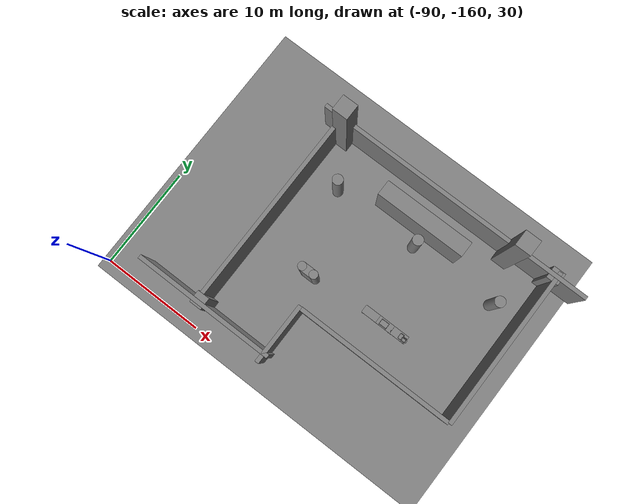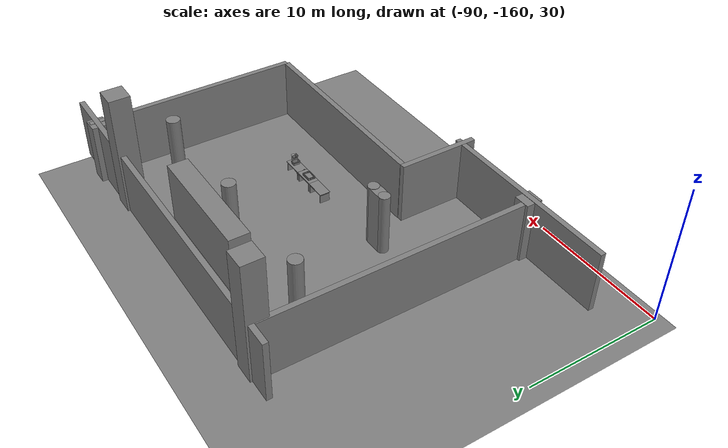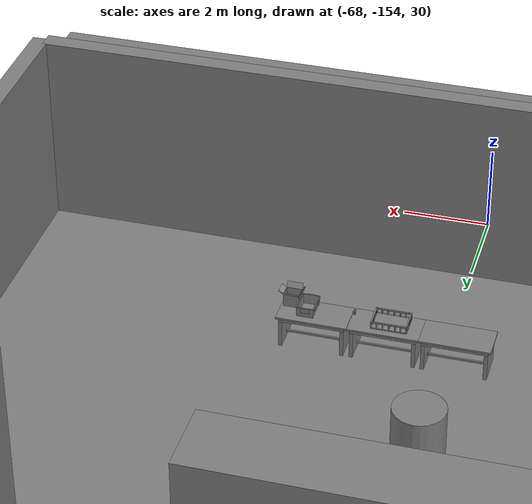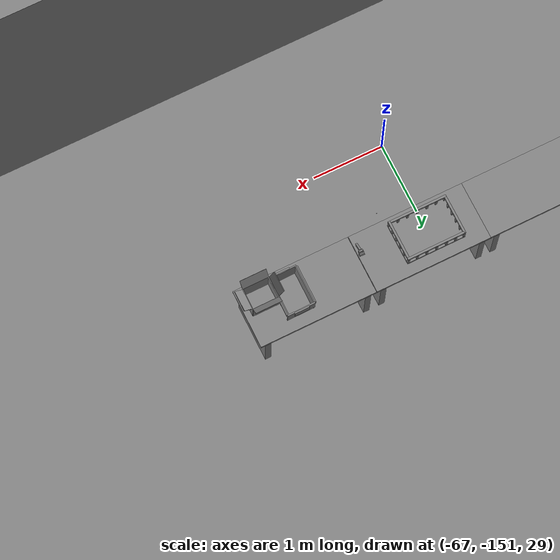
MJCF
<mujoco>
    <option gravity="0.000000000 0.000000000 -9.810000420" timestep="0.0049999999" integrator="implicitfast" density="1.225" viscosity="1.8000001e-05" noslip_iterations="10" iterations="100" sdf_iterations="50">
        <flag multiccd="disable"/>
    </option>
    <size memory="1000M"/>
    <compiler coordinate="local"/>
    <worldbody>
        <light cutoff="30" pos="0 1 1" dir="0 -1 -2"/>
        <light cutoff="30" pos="0 -1 1" dir="0 1 -2"/>
        <body pos="-64.866622925 -149.383972168 30.183746338" euler="89.999992371 89.999946594 0.000000000" name="openloong_gripper_2f85_fix_base_usda_bluebox_01">
            <geom contype="1" conaffinity="1" density="1000" type="box" material="" rgba="0.500000000 0.500000000 0.500000000 1.000000000" solimp="0.899999976 0.949999988 0.001000000" friction="1.000000000 0.005000000 0.000100000" solref="0.020000000 1.000000000" margin="0" condim="3" group="0" pos="0.276596069 0.187225342 0.000061035" quat="0.707107008 0.000077501 0.707106471 0.000077456" size="0.100000001 0.057999998 0.010000000" name="openloong_gripper_2f85_fix_base_usda_geom_6FE589B9_D18B_4F99_9200_BB32CA3C9EE3"/>
            <geom contype="1" conaffinity="1" density="1000" type="box" material="" rgba="0.500000000 0.500000000 0.500000000 1.000000000" solimp="0.899999976 0.949999988 0.001000000" friction="1.000000000 0.005000000 0.000100000" solref="0.020000000 1.000000000" margin="0" condim="3" group="0" pos="0.000000000 0.002883911 0.000000000" quat="1.000000000 0.000000000 0.000000000 0.000000000" size="0.254000008 0.003000000 0.172000006" name="openloong_gripper_2f85_fix_base_usda_geom_06E4AC49_53EF_4B73_A5A3_2D665DB0538D"/>
            <geom contype="1" conaffinity="1" density="1000" type="box" material="" rgba="0.500000000 0.500000000 0.500000000 1.000000000" solimp="0.899999976 0.949999988 0.001000000" friction="1.000000000 0.005000000 0.000100000" solref="0.020000000 1.000000000" margin="0" condim="3" group="0" pos="0.000015259 0.124874115 0.173477173" quat="0.999796450 0.020176515 -0.000000015 0.000000030" size="0.259999990 0.119999997 0.007000000" name="openloong_gripper_2f85_fix_base_usda_geom_A99C23E8_3EF3_43C2_9830_0512F81AE681"/>
            <geom contype="1" conaffinity="1" density="1000" type="box" material="" rgba="0.500000000 0.500000000 0.500000000 1.000000000" solimp="0.899999976 0.949999988 0.001000000" friction="1.000000000 0.005000000 0.000100000" solref="0.020000000 1.000000000" margin="0" condim="3" group="0" pos="0.000015259 0.124874115 -0.173477173" quat="0.999796450 -0.020176545 -0.000000015 0.000000000" size="0.259999990 0.119999997 0.007000000" name="openloong_gripper_2f85_fix_base_usda_geom_200EEDF8_BF34_4C9F_BC3E_CE80C40C28AE"/>
            <geom contype="1" conaffinity="1" density="1000" type="box" material="" rgba="0.500000000 0.500000000 0.500000000 1.000000000" solimp="0.899999976 0.949999988 0.001000000" friction="1.000000000 0.005000000 0.000100000" solref="0.020000000 1.000000000" margin="0" condim="3" group="0" pos="0.000015259 0.214012146 0.188980103" quat="0.999913096 0.013176724 0.000000015 0.000000000" size="0.259999990 0.029999999 0.012500000" name="openloong_gripper_2f85_fix_base_usda_geom_F3AD46F1_2FF1_4433_8EF8_250251697339"/>
            <geom contype="1" conaffinity="1" density="1000" type="box" material="" rgba="0.500000000 0.500000000 0.500000000 1.000000000" solimp="0.899999976 0.949999988 0.001000000" friction="1.000000000 0.005000000 0.000100000" solref="0.020000000 1.000000000" margin="0" condim="3" group="0" pos="-0.258346558 0.125289917 0.001876831" quat="0.702796996 -0.020792052 0.710783184 0.020769238" size="0.189999998 0.119999997 0.009000000" name="openloong_gripper_2f85_fix_base_usda_geom_9BBA8E01_5B16_46C5_AFF1_76CB9E5C7D3A"/>
            <geom contype="1" conaffinity="1" density="1000" type="box" material="" rgba="0.500000000 0.500000000 0.500000000 1.000000000" solimp="0.899999976 0.949999988 0.001000000" friction="1.000000000 0.005000000 0.000100000" solref="0.020000000 1.000000000" margin="0" condim="3" group="0" pos="0.000015259 0.214012146 -0.188980103" quat="0.999913096 -0.013176769 0.000000030 0.000000015" size="0.259999990 0.029999999 0.012500000" name="openloong_gripper_2f85_fix_base_usda_geom_6DC72873_D8D1_4D32_86A3_A6988880E50C"/>
            <geom contype="1" conaffinity="1" density="1000" type="box" material="" rgba="0.500000000 0.500000000 0.500000000 1.000000000" solimp="0.899999976 0.949999988 0.001000000" friction="1.000000000 0.005000000 0.000100000" solref="0.020000000 1.000000000" margin="0" condim="3" group="0" pos="-0.276596069 0.187225342 0.000061035" quat="0.707106650 0.000077441 0.707106709 0.000077456" size="0.100000001 0.057999998 0.010000000" name="openloong_gripper_2f85_fix_base_usda_geom_23860E6D_EFB3_4E23_A75E_27218FCC0355"/>
            <geom contype="1" conaffinity="1" density="1000" type="box" material="" rgba="0.500000000 0.500000000 0.500000000 1.000000000" solimp="0.899999976 0.949999988 0.001000000" friction="1.000000000 0.005000000 0.000100000" solref="0.020000000 1.000000000" margin="0" condim="3" group="0" pos="0.258346558 0.125289917 0.001876831" quat="0.702851534 0.018856451 0.710823834 -0.019329429" size="0.189999998 0.119999997 0.009000000" name="openloong_gripper_2f85_fix_base_usda_geom_7DCECFFF_B73C_4152_9068_5A90CE6A0995"/>
            <freejoint name="openloong_gripper_2f85_fix_base_usda_bluebox_01_joint"/>
            <site size="0.005000000 0.005000000 0.005000000" rgba="0.500000000 0.500000000 0.500000000 1.000000000" pos="0.000000000 0.000000000 0.000000000" quat="0.999961913 0.008726534 0.000000000 0.000000000" group="0" type="sphere" name="openloong_gripper_2f85_fix_base_usda_bluebox_01site"/>
        </body>
        <body pos="-64.496299744 -149.491867065 30.235729218" euler="0.000000000 0.000000000 89.999946594" name="openloong_gripper_2f85_fix_base_usda_cardboardbox_01">
            <geom contype="1" conaffinity="1" density="1000" type="box" material="" rgba="0.500000000 0.500000000 0.500000000 1.000000000" solimp="0.899999976 0.949999988 0.001000000" friction="1.000000000 0.005000000 0.000100000" solref="0.020000000 1.000000000" margin="0" condim="3" group="0" pos="-0.003166199 -0.004086494 0.005052090" quat="1.000000000 0.000000000 0.000000000 0.000000000" size="0.142499998 0.177500010 0.005000000" name="openloong_gripper_2f85_fix_base_usda_geom_76E68517_C7C0_4150_A1AC_026396A03C89"/>
            <geom contype="1" conaffinity="1" density="1000" type="box" material="" rgba="0.500000000 0.500000000 0.500000000 1.000000000" solimp="0.899999976 0.949999988 0.001000000" friction="1.000000000 0.005000000 0.000100000" solref="0.020000000 1.000000000" margin="0" condim="3" group="0" pos="-0.003166199 0.170316696 0.150570869" quat="1.000000000 0.000000000 0.000000000 0.000000000" size="0.142499998 0.005000000 0.149999991" name="openloong_gripper_2f85_fix_base_usda_geom_8A540A64_8B41_4560_9B1E_F0D833AE4CA5"/>
            <geom contype="1" conaffinity="1" density="1000" type="box" material="" rgba="0.500000000 0.500000000 0.500000000 1.000000000" solimp="0.899999976 0.949999988 0.001000000" friction="1.000000000 0.005000000 0.000100000" solref="0.020000000 1.000000000" margin="0" condim="3" group="0" pos="-0.147399902 -0.005307198 0.150570869" quat="1.000000000 0.000000000 0.000000000 0.000000000" size="0.005000000 0.177500010 0.149999991" name="openloong_gripper_2f85_fix_base_usda_geom_B49BB0ED_5BDD_4CFA_9DE4_456EE212E890"/>
            <geom contype="1" conaffinity="1" density="1000" type="box" material="" rgba="0.500000000 0.500000000 0.500000000 1.000000000" solimp="0.899999976 0.949999988 0.001000000" friction="1.000000000 0.005000000 0.000100000" solref="0.020000000 1.000000000" margin="0" condim="3" group="0" pos="0.140275955 -0.005307198 0.150570869" quat="1.000000000 0.000000000 0.000000000 0.000000000" size="0.005000000 0.177500010 0.149999991" name="openloong_gripper_2f85_fix_base_usda_geom_0C672FBD_5C87_489A_ABD7_67E4957AF19D"/>
            <geom contype="1" conaffinity="1" density="1000" type="box" material="" rgba="0.500000000 0.500000000 0.500000000 1.000000000" solimp="0.899999976 0.949999988 0.001000000" friction="1.000000000 0.005000000 0.000100000" solref="0.020000000 1.000000000" margin="0" condim="3" group="0" pos="-0.003166199 -0.181550980 0.150570869" quat="1.000000000 0.000000000 0.000000000 0.000000000" size="0.142499998 0.005000000 0.149999991" name="openloong_gripper_2f85_fix_base_usda_geom_BFBDC58C_7221_46F5_8B06_B7FCD5577971"/>
            <freejoint name="openloong_gripper_2f85_fix_base_usda_cardboardbox_01_joint"/>
            <site size="0.005000000 0.005000000 0.005000000" rgba="0.500000000 0.500000000 0.500000000 1.000000000" pos="0.000000000 0.000000000 0.000000000" quat="0.999961913 0.008726535 0.000000000 0.000000000" group="0" type="sphere" name="openloong_gripper_2f85_fix_base_usda_site_670C7062_D96F_4CEF_B33D_AF3473655FDB"/>
            <body pos="0.139160156 -0.004048347 0.301930904" euler="-179.999954224 49.383502960 179.999954224" name="openloong_gripper_2f85_fix_base_usda_A1_006">
                <geom contype="1" conaffinity="1" density="1000" type="box" material="" rgba="0.500000000 0.500000000 0.500000000 1.000000000" solimp="0.899999976 0.949999988 0.001000000" friction="1.000000000 0.005000000 0.000100000" solref="0.020000000 1.000000000" margin="0" condim="3" group="0" pos="-0.071587563 0.000009537 0.001745224" quat="0.999999881 0.000000000 0.000000000 0.000000000" size="0.071249999 0.179999992 0.002500000" name="openloong_gripper_2f85_fix_base_usda_geom_134D26DE_DD5A_451F_B91D_856A54DC2F7B"/>
                <joint armature="0" stiffness="0.07" damping="0.0099999998" axis="0.000000 1.000000 0.000000" type="hinge" name="openloong_gripper_2f85_fix_base_usda_A1_006"/>
            </body>
            <body pos="-0.145902634 -0.004086494 0.301938057" euler="-180.000000000 -60.000011444 -180.000000000" name="openloong_gripper_2f85_fix_base_usda_A2_006">
                <geom contype="1" conaffinity="1" density="1000" type="box" material="" rgba="0.500000000 0.500000000 0.500000000 1.000000000" solimp="0.899999976 0.949999988 0.001000000" friction="1.000000000 0.005000000 0.000100000" solref="0.020000000 1.000000000" margin="0" condim="3" group="0" pos="0.071268082 0.000009537 0.002717972" quat="0.000002921 0.000000000 -0.000000030 0.999999881" size="0.071249999 0.179999992 0.002500000" name="openloong_gripper_2f85_fix_base_usda_geom_556C8BED_E17E_4E13_8B2F_17D85F95A7AB"/>
                <joint armature="0" stiffness="0.07" damping="0.0099999998" axis="0.000000 1.000000 0.000000" type="hinge" name="openloong_gripper_2f85_fix_base_usda_A2_006"/>
            </body>
            <body pos="-0.003385544 0.175991058 0.301930904" euler="-125.858116150 -0.000004561 0.000002331" name="openloong_gripper_2f85_fix_base_usda_B2_006">
                <geom contype="1" conaffinity="1" density="1000" type="box" material="" rgba="0.500000000 0.500000000 0.500000000 1.000000000" solimp="0.899999976 0.949999988 0.001000000" friction="1.000000000 0.005000000 0.000100000" solref="0.020000000 1.000000000" margin="0" condim="3" group="0" pos="0.000009537 -0.070939064 -0.002470016" quat="0.999614120 0.027776197 -0.000000015 0.000000030" size="0.137500003 0.064999998 0.005000000" name="openloong_gripper_2f85_fix_base_usda_geom_63B4C8F5_9244_478C_9583_B4513A0DF67C"/>
                <joint armature="0" stiffness="0.07" damping="0.0099999998" axis="1.000000 0.000000 0.000000" type="hinge" name="openloong_gripper_2f85_fix_base_usda_B2_006"/>
            </body>
            <body pos="-0.003385544 -0.184140205 0.301938057" euler="147.805557251 0.000000000 0.000000000" name="openloong_gripper_2f85_fix_base_usda_B1_006">
                <geom contype="1" conaffinity="1" density="1000" type="box" material="" rgba="0.500000000 0.500000000 0.500000000 1.000000000" solimp="0.899999976 0.949999988 0.001000000" friction="1.000000000 0.005000000 0.000100000" solref="0.020000000 1.000000000" margin="0" condim="3" group="0" pos="-0.000028610 0.070202351 -0.002703667" quat="0.999614179 -0.027776167 0.000000000 0.000000000" size="0.137500003 0.064999998 0.005000000" name="openloong_gripper_2f85_fix_base_usda_geom_E199E9C4_83E4_411A_A723_7FA19CAE0131"/>
                <joint armature="0" stiffness="0.07" damping="0.0099999998" axis="1.000000 0.000000 0.000000" type="hinge" name="openloong_gripper_2f85_fix_base_usda_B1_006"/>
            </body>
        </body>
        <body pos="-65.882858276 -149.481979370 30.229999542" euler="-64.487716675 0.000000000 0.000000000" name="openloong_gripper_2f85_fix_base_usda_Barcode">
            <geom contype="1" conaffinity="1" density="1000" type="box" material="" rgba="0.500000000 0.500000000 0.500000000 1.000000000" solimp="0.899999976 0.949999988 0.001000000" friction="1.000000000 0.005000000 0.000100000" solref="0.020000000 1.000000000" margin="0" condim="3" group="0" pos="0.000000000 0.013038635 0.001419067" quat="0.000000000 0.000000000 0.000000000 1.000000119" size="0.034000002 0.010000000 0.017999999" name="openloong_gripper_2f85_fix_base_usda_geom_30C348BA_3166_4720_8E25_7E768212F3D6"/>
            <geom contype="1" conaffinity="1" density="1000" type="box" material="" rgba="0.500000000 0.500000000 0.500000000 1.000000000" solimp="0.899999976 0.949999988 0.001000000" friction="1.000000000 0.005000000 0.000100000" solref="0.020000000 1.000000000" margin="0" condim="3" group="0" pos="0.000000000 -0.035301208 -0.007095337" quat="0.000000000 0.000000000 -0.043619365 0.999048233" size="0.028999999 0.010000000 0.020000000" name="openloong_gripper_2f85_fix_base_usda_geom_E31EA157_B439_445B_BB12_448859BE41FD"/>
            <geom contype="1" conaffinity="1" density="1000" type="box" material="" rgba="0.500000000 0.500000000 0.500000000 1.000000000" solimp="0.899999976 0.949999988 0.001000000" friction="1.000000000 0.005000000 0.000100000" solref="0.020000000 1.000000000" margin="0" condim="3" group="0" pos="0.000000000 -0.043411255 -0.011749268" quat="0.922262907 0.386563420 0.000000000 0.000000000" size="0.026000001 0.010000000 0.020000000" name="openloong_gripper_2f85_fix_base_usda_geom_6DF01A15_433E_4B88_8465_D0356390DA12"/>
            <geom contype="1" conaffinity="1" density="1000" type="box" material="" rgba="0.500000000 0.500000000 0.500000000 1.000000000" solimp="0.899999976 0.949999988 0.001000000" friction="1.000000000 0.005000000 0.000100000" solref="0.020000000 1.000000000" margin="0" condim="3" group="0" pos="0.000000000 -0.016967773 -0.031860352" quat="0.000000000 0.000000000 0.000000000 1.000000119" size="0.008000000 0.010000000 0.013000000" name="openloong_gripper_2f85_fix_base_usda_geom_7B5353FE_FE72_4AA1_B354_CD0C4836F0ED"/>
            <geom contype="1" conaffinity="1" density="1000" type="box" material="" rgba="0.500000000 0.500000000 0.500000000 1.000000000" solimp="0.899999976 0.949999988 0.001000000" friction="1.000000000 0.005000000 0.000100000" solref="0.020000000 1.000000000" margin="0" condim="3" group="0" pos="0.000000000 -0.001869202 0.000312805" quat="0.953716993 0.300705761 0.000000000 0.000000000" size="0.032000002 0.010000000 0.018999999" name="openloong_gripper_2f85_fix_base_usda_geom_0F270009_4821_4034_9CCA_D0F38036D61D"/>
            <geom contype="1" conaffinity="1" density="1000" type="box" material="" rgba="0.500000000 0.500000000 0.500000000 1.000000000" solimp="0.899999976 0.949999988 0.001000000" friction="1.000000000 0.005000000 0.000100000" solref="0.020000000 1.000000000" margin="0" condim="3" group="0" pos="0.000000000 -0.019531250 -0.003173828" quat="0.953716993 0.300705761 0.000000000 0.000000000" size="0.030999999 0.010000000 0.020000000" name="openloong_gripper_2f85_fix_base_usda_geom_6EEEFF78_8D02_4867_8E5C_469C2485CEF5"/>
            <geom contype="1" conaffinity="1" density="1000" type="box" material="" rgba="0.500000000 0.500000000 0.500000000 1.000000000" solimp="0.899999976 0.949999988 0.001000000" friction="1.000000000 0.005000000 0.000100000" solref="0.020000000 1.000000000" margin="0" condim="3" group="0" pos="0.000000000 -0.035301208 -0.007095337" quat="0.953716993 0.300705761 0.000000000 0.000000000" size="0.028999999 0.010000000 0.020000000" name="openloong_gripper_2f85_fix_base_usda_geom_3CC79231_F6E0_47D5_9F78_A55FDA3914C0"/>
            <geom contype="1" conaffinity="1" density="1000" type="box" material="" rgba="0.500000000 0.500000000 0.500000000 1.000000000" solimp="0.899999976 0.949999988 0.001000000" friction="1.000000000 0.005000000 0.000100000" solref="0.020000000 1.000000000" margin="0" condim="3" group="0" pos="0.000000000 -0.042617798 -0.071121216" quat="0.000000000 0.000000000 0.000000000 1.000000119" size="0.013000000 0.021000000 0.059999999" name="openloong_gripper_2f85_fix_base_usda_geom_2135A9E5_1F8E_44E6_9E61_7545B7617DE2"/>
            <freejoint name="openloong_gripper_2f85_fix_base_usda_Barcode_joint"/>
            <site size="0.005000000 0.005000000 0.005000000" rgba="0.500000000 0.500000000 0.500000000 1.000000000" pos="0.000000000 0.000000000 0.000000000" quat="1.000000000 0.000000000 0.000000000 0.000000000" group="0" type="sphere" name="openloong_gripper_2f85_fix_base_usda_Barcode_site"/>
        </body>
        <body pos="-66.745018005 -149.392349243 30.184000015" euler="0.000000000 0.000000000 89.999946594" name="[22331488078375]_Basket_01">
            <geom contype="1" conaffinity="1" density="1000" type="box" material="" rgba="0.500000000 0.500000000 0.500000000 1.000000000" solimp="0.899999976 0.949999988 0.001000000" friction="1.000000000 0.005000000 0.000100000" solref="0.020000000 1.000000000" margin="0" condim="3" group="0" pos="-0.052425385 0.389207840 0.089787483" quat="0.707107008 0.000000000 0.000000000 0.707106411" size="0.014249999 0.014249999 0.059999999" name="[22331488078375]_geom_FF2C27C3_91D2_49F5_AD5C_FEE9D25A6F2D"/>
            <geom contype="1" conaffinity="1" density="1000" type="box" material="" rgba="0.500000000 0.500000000 0.500000000 1.000000000" solimp="0.899999976 0.949999988 0.001000000" friction="1.000000000 0.005000000 0.000100000" solref="0.020000000 1.000000000" margin="0" condim="3" group="0" pos="0.264015198 -0.133043289 0.089787483" quat="0.707107008 0.000000000 0.000000000 0.707106411" size="0.014249999 0.014249999 0.059999999" name="[22331488078375]_geom_16FEF1D0_2FFF_47C0_A6FD_14E33BF5461F"/>
            <geom contype="1" conaffinity="1" density="1000" type="box" material="" rgba="0.500000000 0.500000000 0.500000000 1.000000000" solimp="0.899999976 0.949999988 0.001000000" friction="1.000000000 0.005000000 0.000100000" solref="0.020000000 1.000000000" margin="0" condim="3" group="0" pos="-0.264015198 -0.265548706 0.089793205" quat="0.707107008 0.000000000 0.000000000 0.707106411" size="0.014249999 0.014249999 0.059999999" name="[22331488078375]_geom_5E3D634F_035D_4852_9813_6113AE69CCC1"/>
            <geom contype="1" conaffinity="1" density="1000" type="box" material="" rgba="0.500000000 0.500000000 0.500000000 1.000000000" solimp="0.899999976 0.949999988 0.001000000" friction="1.000000000 0.005000000 0.000100000" solref="0.020000000 1.000000000" margin="0" condim="3" group="0" pos="-0.160263062 -0.389322281 0.089793205" quat="0.707107008 0.000000000 0.000000000 0.707106411" size="0.014249999 0.014249999 0.059999999" name="[22331488078375]_geom_85A42524_4AEC_4369_8EDD_CC4C791AD008"/>
            <geom contype="1" conaffinity="1" density="1000" type="box" material="" rgba="0.500000000 0.500000000 0.500000000 1.000000000" solimp="0.899999976 0.949999988 0.001000000" friction="1.000000000 0.005000000 0.000100000" solref="0.020000000 1.000000000" margin="0" condim="3" group="0" pos="0.162265778 -0.389322281 0.089787483" quat="0.707107008 0.000000000 0.000000000 0.707106411" size="0.014249999 0.014249999 0.059999999" name="[22331488078375]_geom_9F9C1C5C_21DE_46AD_86B9_4E6B4CCE06B9"/>
            <geom contype="1" conaffinity="1" density="1000" type="box" material="" rgba="0.500000000 0.500000000 0.500000000 1.000000000" solimp="0.899999976 0.949999988 0.001000000" friction="1.000000000 0.005000000 0.000100000" solref="0.020000000 1.000000000" margin="0" condim="3" group="0" pos="0.264015198 0.389207840 0.089787483" quat="0.707107008 0.000000000 0.000000000 0.707106411" size="0.014249999 0.014249999 0.059999999" name="[22331488078375]_geom_6AABE1A2_F02C_459B_843F_1A597DB5946C"/>
            <geom contype="1" conaffinity="1" density="1000" type="box" material="" rgba="0.500000000 0.500000000 0.500000000 1.000000000" solimp="0.899999976 0.949999988 0.001000000" friction="1.000000000 0.005000000 0.000100000" solref="0.020000000 1.000000000" margin="0" condim="3" group="0" pos="-0.264015198 -0.133043289 0.089793205" quat="0.707107008 0.000000000 0.000000000 0.707106411" size="0.014249999 0.014249999 0.059999999" name="[22331488078375]_geom_1A15105D_1729_4C2B_96C7_1F976B1EAAB4"/>
            <geom contype="1" conaffinity="1" density="1000" type="box" material="" rgba="0.500000000 0.500000000 0.500000000 1.000000000" solimp="0.899999976 0.949999988 0.001000000" friction="1.000000000 0.005000000 0.000100000" solref="0.020000000 1.000000000" margin="0" condim="3" group="0" pos="-0.264026642 0.269256592 0.089793205" quat="0.707107008 0.000000000 0.000000000 0.707106411" size="0.014249999 0.014249999 0.059999999" name="[22331488078375]_geom_05C0AF36_B3DC_4F69_9892_1D35CDE036F7"/>
            <geom contype="1" conaffinity="1" density="1000" type="box" material="" rgba="0.500000000 0.500000000 0.500000000 1.000000000" solimp="0.899999976 0.949999988 0.001000000" friction="1.000000000 0.005000000 0.000100000" solref="0.020000000 1.000000000" margin="0" condim="3" group="0" pos="0.054462433 0.389207840 0.089787483" quat="0.707107008 0.000000000 0.000000000 0.707106411" size="0.014249999 0.014249999 0.059999999" name="[22331488078375]_geom_57A3CB70_8BFC_444A_8DB4_E7CC6C152322"/>
            <geom contype="1" conaffinity="1" density="1000" type="box" material="" rgba="0.500000000 0.500000000 0.500000000 1.000000000" solimp="0.899999976 0.949999988 0.001000000" friction="1.000000000 0.005000000 0.000100000" solref="0.020000000 1.000000000" margin="0" condim="3" group="0" pos="0.054462433 -0.389322281 0.089787483" quat="0.707107008 0.000000000 0.000000000 0.707106411" size="0.014249999 0.014249999 0.059999999" name="[22331488078375]_geom_69FE63A1_4B41_4468_9B57_C012CC9CDCFE"/>
            <geom contype="1" conaffinity="1" density="1000" type="box" material="" rgba="0.500000000 0.500000000 0.500000000 1.000000000" solimp="0.899999976 0.949999988 0.001000000" friction="1.000000000 0.005000000 0.000100000" solref="0.020000000 1.000000000" margin="0" condim="3" group="0" pos="0.264015198 0.269256592 0.089793205" quat="0.707107008 0.000000000 0.000000000 0.707106411" size="0.014249999 0.014249999 0.059999999" name="[22331488078375]_geom_C9A9C6A6_F674_409F_8E52_9DEFBF124A86"/>
            <geom contype="1" conaffinity="1" density="1000" type="box" material="" rgba="0.500000000 0.500000000 0.500000000 1.000000000" solimp="0.899999976 0.949999988 0.001000000" friction="1.000000000 0.005000000 0.000100000" solref="0.020000000 1.000000000" margin="0" condim="3" group="0" pos="0.264015198 -0.389322281 0.089787483" quat="0.707107008 0.000000000 0.000000000 0.707106411" size="0.014249999 0.014249999 0.059999999" name="[22331488078375]_geom_1B1E7B22_3710_414F_960F_9936226E69F5"/>
            <geom contype="1" conaffinity="1" density="1000" type="box" material="" rgba="0.500000000 0.500000000 0.500000000 1.000000000" solimp="0.899999976 0.949999988 0.001000000" friction="1.000000000 0.005000000 0.000100000" solref="0.020000000 1.000000000" margin="0" condim="3" group="0" pos="0.000000000 0.000000000 0.015998840" quat="0.707107008 0.000000000 0.000000000 0.707106411" size="0.403499991 0.279000014 0.015750000" name="[22331488078375]_geom_2DB27E59_CDE3_4899_B418_FE7ACF9F3DDB"/>
            <geom contype="1" conaffinity="1" density="1000" type="box" material="" rgba="0.500000000 0.500000000 0.500000000 1.000000000" solimp="0.899999976 0.949999988 0.001000000" friction="1.000000000 0.005000000 0.000100000" solref="0.020000000 1.000000000" margin="0" condim="3" group="0" pos="0.000000000 -0.389476776 0.163619041" quat="0.707107008 0.000000000 0.000000000 0.707106411" size="0.015000000 0.277500004 0.015750000" name="[22331488078375]_geom_5782B729_5BAC_4F3E_96AD_5C07EA4F37E8"/>
            <geom contype="1" conaffinity="1" density="1000" type="box" material="" rgba="0.500000000 0.500000000 0.500000000 1.000000000" solimp="0.899999976 0.949999988 0.001000000" friction="1.000000000 0.005000000 0.000100000" solref="0.020000000 1.000000000" margin="0" condim="3" group="0" pos="0.162265778 0.389207840 0.089787483" quat="0.707107008 0.000000000 0.000000000 0.707106411" size="0.014249999 0.014249999 0.059999999" name="[22331488078375]_geom_C2D0C135_EE4B_4D39_BD28_4FB82123488D"/>
            <geom contype="1" conaffinity="1" density="1000" type="box" material="" rgba="0.500000000 0.500000000 0.500000000 1.000000000" solimp="0.899999976 0.949999988 0.001000000" friction="1.000000000 0.005000000 0.000100000" solref="0.020000000 1.000000000" margin="0" condim="3" group="0" pos="0.000000000 0.389471054 0.163619041" quat="0.707107008 0.000000000 0.000000000 0.707106411" size="0.015000000 0.277500004 0.015750000" name="[22331488078375]_geom_8C847DDD_B8F9_4E3B_98C1_D87F1D1FBA4C"/>
            <geom contype="1" conaffinity="1" density="1000" type="box" material="" rgba="0.500000000 0.500000000 0.500000000 1.000000000" solimp="0.899999976 0.949999988 0.001000000" friction="1.000000000 0.005000000 0.000100000" solref="0.020000000 1.000000000" margin="0" condim="3" group="0" pos="-0.263511658 0.000000000 0.163619041" quat="0.707107008 0.000000000 0.000000000 0.707106411" size="0.403499991 0.015000000 0.015750000" name="[22331488078375]_geom_A9291C64_A1DE_4F0A_AE3A_CA72DE5CBFF9"/>
            <geom contype="1" conaffinity="1" density="1000" type="box" material="" rgba="0.500000000 0.500000000 0.500000000 1.000000000" solimp="0.899999976 0.949999988 0.001000000" friction="1.000000000 0.005000000 0.000100000" solref="0.020000000 1.000000000" margin="0" condim="3" group="0" pos="-0.264015198 0.141334534 0.089793205" quat="0.707107008 0.000000000 0.000000000 0.707106411" size="0.014249999 0.014249999 0.059999999" name="[22331488078375]_geom_FEC1FF67_02CB_4C0A_9B0D_739BD4ABED49"/>
            <geom contype="1" conaffinity="1" density="1000" type="box" material="" rgba="0.500000000 0.500000000 0.500000000 1.000000000" solimp="0.899999976 0.949999988 0.001000000" friction="1.000000000 0.005000000 0.000100000" solref="0.020000000 1.000000000" margin="0" condim="3" group="0" pos="0.264015198 -0.265548706 0.089787483" quat="0.707107008 0.000000000 0.000000000 0.707106411" size="0.014249999 0.014249999 0.059999999" name="[22331488078375]_geom_26269C23_57F3_42C0_AE72_7910EE5A617F"/>
            <geom contype="1" conaffinity="1" density="1000" type="box" material="" rgba="0.500000000 0.500000000 0.500000000 1.000000000" solimp="0.899999976 0.949999988 0.001000000" friction="1.000000000 0.005000000 0.000100000" solref="0.020000000 1.000000000" margin="0" condim="3" group="0" pos="-0.160263062 0.389207840 0.089787483" quat="0.707107008 0.000000000 0.000000000 0.707106411" size="0.014249999 0.014249999 0.059999999" name="[22331488078375]_geom_E095F93F_B625_4CA7_B3EB_8FF0BBA5701C"/>
            <geom contype="1" conaffinity="1" density="1000" type="box" material="" rgba="0.500000000 0.500000000 0.500000000 1.000000000" solimp="0.899999976 0.949999988 0.001000000" friction="1.000000000 0.005000000 0.000100000" solref="0.020000000 1.000000000" margin="0" condim="3" group="0" pos="-0.052425385 -0.389322281 0.089787483" quat="0.707107008 0.000000000 0.000000000 0.707106411" size="0.014249999 0.014249999 0.059999999" name="[22331488078375]_geom_EABD8B05_6268_4000_A432_A7A075F252BC"/>
            <geom contype="1" conaffinity="1" density="1000" type="box" material="" rgba="0.500000000 0.500000000 0.500000000 1.000000000" solimp="0.899999976 0.949999988 0.001000000" friction="1.000000000 0.005000000 0.000100000" solref="0.020000000 1.000000000" margin="0" condim="3" group="0" pos="-0.264026642 -0.389322281 0.089793205" quat="0.707107008 0.000000000 0.000000000 0.707106411" size="0.014249999 0.014249999 0.059999999" name="[22331488078375]_geom_DF524076_7576_4D0C_9D66_CF91BF5979C6"/>
            <geom contype="1" conaffinity="1" density="1000" type="box" material="" rgba="0.500000000 0.500000000 0.500000000 1.000000000" solimp="0.899999976 0.949999988 0.001000000" friction="1.000000000 0.005000000 0.000100000" solref="0.020000000 1.000000000" margin="0" condim="3" group="0" pos="0.264015198 0.141334534 0.089787483" quat="0.707107008 0.000000000 0.000000000 0.707106411" size="0.014249999 0.014249999 0.059999999" name="[22331488078375]_geom_23F2A39B_1EA9_4F8E_8FE0_95BF40BA4F87"/>
            <geom contype="1" conaffinity="1" density="1000" type="box" material="" rgba="0.500000000 0.500000000 0.500000000 1.000000000" solimp="0.899999976 0.949999988 0.001000000" friction="1.000000000 0.005000000 0.000100000" solref="0.020000000 1.000000000" margin="0" condim="3" group="0" pos="-0.264015198 0.389207840 0.089793205" quat="0.707107008 0.000000000 0.000000000 0.707106411" size="0.014249999 0.014249999 0.059999999" name="[22331488078375]_geom_84A1D237_2952_42D1_AA21_6916B6DF3BA3"/>
            <geom contype="1" conaffinity="1" density="1000" type="box" material="" rgba="0.500000000 0.500000000 0.500000000 1.000000000" solimp="0.899999976 0.949999988 0.001000000" friction="1.000000000 0.005000000 0.000100000" solref="0.020000000 1.000000000" margin="0" condim="3" group="0" pos="0.264015198 0.004480362 0.089787483" quat="0.707107008 0.000000000 0.000000000 0.707106411" size="0.014249999 0.014249999 0.059999999" name="[22331488078375]_geom_D94024EE_1AFB_4EFD_A274_39191A8441A6"/>
            <geom contype="1" conaffinity="1" density="1000" type="box" material="" rgba="0.500000000 0.500000000 0.500000000 1.000000000" solimp="0.899999976 0.949999988 0.001000000" friction="1.000000000 0.005000000 0.000100000" solref="0.020000000 1.000000000" margin="0" condim="3" group="0" pos="0.263694763 -0.000011444 0.163619041" quat="0.707107008 0.000000000 0.000000000 0.707106411" size="0.403499991 0.015000000 0.015750000" name="[22331488078375]_geom_17A15AA6_05A7_460E_9941_67263F49FA02"/>
            <geom contype="1" conaffinity="1" density="1000" type="box" material="" rgba="0.500000000 0.500000000 0.500000000 1.000000000" solimp="0.899999976 0.949999988 0.001000000" friction="1.000000000 0.005000000 0.000100000" solref="0.020000000 1.000000000" margin="0" condim="3" group="0" pos="-0.264015198 0.004480362 0.089793205" quat="0.707107008 0.000000000 0.000000000 0.707106411" size="0.014249999 0.014249999 0.059999999" name="[22331488078375]_geom_5425B5F5_871B_4EA8_929C_229EDB3B3852"/>
            <freejoint name="[22331488078375]_joint_D694F41B_6F91_4B47_986A_B93355AF51C1"/>
        </body>
        <body pos="0.000000000 0.000000000 0.000000000" euler="0.000000000 0.000000000 0.000000000" name="Static Objects_Static Objects">
            <geom contype="1" conaffinity="1" density="1000" type="box" material="" rgba="0.500000000 0.500000000 0.500000000 1.000000000" solimp="0.899999976 0.949999988 0.001000000" friction="1.000000000 0.005000000 0.000100000" solref="0.020000000 1.000000000" margin="0" condim="3" group="0" pos="-67.544113159 -149.365814209 29.727830887" quat="0.500000417 0.499999970 0.499999553 0.499999970" size="0.381000012 0.319999993 0.041000001" name="Static Objects_geom_F534D941_E8DF_4139_AFC2_08B0F0623573"/>
            <geom contype="1" conaffinity="1" density="1000" type="box" material="" rgba="0.500000000 0.500000000 0.500000000 1.000000000" solimp="0.899999976 0.949999988 0.001000000" friction="1.000000000 0.005000000 0.000100000" solref="0.020000000 1.000000000" margin="0" condim="3" group="0" pos="-68.239501953 -149.365814209 30.086868286" quat="0.500000417 0.499999970 0.499999553 0.499999970" size="0.370999992 0.039500002 0.745000005" name="Static Objects_geom_D9C2174D_F060_4EBD_A49E_5534CAE81CA5"/>
            <geom contype="1" conaffinity="1" density="1000" type="box" material="" rgba="0.500000000 0.500000000 0.500000000 1.000000000" solimp="0.899999976 0.949999988 0.001000000" friction="1.000000000 0.005000000 0.000100000" solref="0.020000000 1.000000000" margin="0" condim="3" group="0" pos="-68.239501953 -149.365814209 30.147235870" quat="0.500000417 0.499999970 0.499999553 0.499999970" size="0.400000006 0.022000000 0.800000012" name="Static Objects_geom_08E49825_790B_49CA_95AD_AD4C0E9D7338"/>
            <geom contype="1" conaffinity="1" density="1000" type="box" material="" rgba="0.500000000 0.500000000 0.500000000 1.000000000" solimp="0.899999976 0.949999988 0.001000000" friction="1.000000000 0.005000000 0.000100000" solref="0.020000000 1.000000000" margin="0" condim="3" group="0" pos="-68.934890747 -149.365814209 29.727830887" quat="0.500000417 0.499999970 0.499999553 0.499999970" size="0.381000012 0.319999993 0.041000001" name="Static Objects_geom_2008C7DB_16F4_4295_AF5C_A3A73B7E3DB2"/>
            <geom contype="1" conaffinity="1" density="1000" type="box" material="" rgba="0.500000000 0.500000000 0.500000000 1.000000000" solimp="0.899999976 0.949999988 0.001000000" friction="1.000000000 0.005000000 0.000100000" solref="0.020000000 1.000000000" margin="0" condim="3" group="0" pos="-68.239501953 -149.365814209 29.561563492" quat="0.500000417 0.499999970 0.499999553 0.499999970" size="0.020000000 0.022000000 0.660000026" name="Static Objects_geom_5372AA01_8EC6_45DF_9016_68A93127357A"/>
            <geom contype="1" conaffinity="1" density="1000" type="box" material="" rgba="0.500000000 0.500000000 0.500000000 1.000000000" solimp="0.899999976 0.949999988 0.001000000" friction="1.000000000 0.005000000 0.000100000" solref="0.020000000 1.000000000" margin="0" condim="3" group="0" pos="-65.945671082 -149.365814209 29.727830887" quat="0.500000417 0.499999970 0.499999553 0.499999970" size="0.381000012 0.319999993 0.041000001" name="Static Objects_geom_0094D8DA_024F_45ED_AB4B_B23E7BB44EAB"/>
            <geom contype="1" conaffinity="1" density="1000" type="box" material="" rgba="0.500000000 0.500000000 0.500000000 1.000000000" solimp="0.899999976 0.949999988 0.001000000" friction="1.000000000 0.005000000 0.000100000" solref="0.020000000 1.000000000" margin="0" condim="3" group="0" pos="-66.641059875 -149.365814209 30.086868286" quat="0.500000417 0.499999970 0.499999553 0.499999970" size="0.370999992 0.039500002 0.745000005" name="Static Objects_geom_1B66AC53_B22A_4119_92B8_23A97CBBEE11"/>
            <geom contype="1" conaffinity="1" density="1000" type="box" material="" rgba="0.500000000 0.500000000 0.500000000 1.000000000" solimp="0.899999976 0.949999988 0.001000000" friction="1.000000000 0.005000000 0.000100000" solref="0.020000000 1.000000000" margin="0" condim="3" group="0" pos="-66.641059875 -149.365814209 30.147235870" quat="0.500000417 0.499999970 0.499999553 0.499999970" size="0.400000006 0.022000000 0.800000012" name="Static Objects_geom_E8E79271_A2BD_4535_97B5_89189BF77682"/>
            <geom contype="1" conaffinity="1" density="1000" type="box" material="" rgba="0.500000000 0.500000000 0.500000000 1.000000000" solimp="0.899999976 0.949999988 0.001000000" friction="1.000000000 0.005000000 0.000100000" solref="0.020000000 1.000000000" margin="0" condim="3" group="0" pos="-67.336448669 -149.365814209 29.727830887" quat="0.500000417 0.499999970 0.499999553 0.499999970" size="0.381000012 0.319999993 0.041000001" name="Static Objects_geom_320912CF_D562_489F_B9CD_AC947020F077"/>
            <geom contype="1" conaffinity="1" density="1000" type="box" material="" rgba="0.500000000 0.500000000 0.500000000 1.000000000" solimp="0.899999976 0.949999988 0.001000000" friction="1.000000000 0.005000000 0.000100000" solref="0.020000000 1.000000000" margin="0" condim="3" group="0" pos="-66.641059875 -149.365814209 29.561563492" quat="0.500000417 0.499999970 0.499999553 0.499999970" size="0.020000000 0.022000000 0.660000026" name="Static Objects_geom_0898553A_1EB4_465C_831F_A37D15ED3690"/>
            <geom contype="1" conaffinity="1" density="1000" type="box" material="" rgba="0.500000000 0.500000000 0.500000000 1.000000000" solimp="0.899999976 0.949999988 0.001000000" friction="1.000000000 0.005000000 0.000100000" solref="0.020000000 1.000000000" margin="0" condim="3" group="0" pos="-64.338577271 -149.365814209 29.727830887" quat="0.500000417 0.499999970 0.499999553 0.499999970" size="0.381000012 0.319999993 0.041000001" name="Static Objects_geom_BBA6C25C_023C_4ADE_9801_B0D13D0DCF30"/>
            <geom contype="1" conaffinity="1" density="1000" type="box" material="" rgba="0.500000000 0.500000000 0.500000000 1.000000000" solimp="0.899999976 0.949999988 0.001000000" friction="1.000000000 0.005000000 0.000100000" solref="0.020000000 1.000000000" margin="0" condim="3" group="0" pos="-65.033966064 -149.365814209 30.086868286" quat="0.500000417 0.499999970 0.499999553 0.499999970" size="0.370999992 0.039500002 0.745000005" name="Static Objects_geom_35838EE3_D5D7_41B7_A610_1110E0D5C8C2"/>
            <geom contype="1" conaffinity="1" density="1000" type="box" material="" rgba="0.500000000 0.500000000 0.500000000 1.000000000" solimp="0.899999976 0.949999988 0.001000000" friction="1.000000000 0.005000000 0.000100000" solref="0.020000000 1.000000000" margin="0" condim="3" group="0" pos="-65.033966064 -149.365814209 30.147235870" quat="0.500000417 0.499999970 0.499999553 0.499999970" size="0.400000006 0.022000000 0.800000012" name="Static Objects_geom_9EB38FE2_94D0_4FF4_8520_D71C1EC88944"/>
            <geom contype="1" conaffinity="1" density="1000" type="box" material="" rgba="0.500000000 0.500000000 0.500000000 1.000000000" solimp="0.899999976 0.949999988 0.001000000" friction="1.000000000 0.005000000 0.000100000" solref="0.020000000 1.000000000" margin="0" condim="3" group="0" pos="-65.729354858 -149.365814209 29.727830887" quat="0.500000417 0.499999970 0.499999553 0.499999970" size="0.381000012 0.319999993 0.041000001" name="Static Objects_geom_E0C20D38_02E9_413C_AEA4_85D9F40B04F6"/>
            <geom contype="1" conaffinity="1" density="1000" type="box" material="" rgba="0.500000000 0.500000000 0.500000000 1.000000000" solimp="0.899999976 0.949999988 0.001000000" friction="1.000000000 0.005000000 0.000100000" solref="0.020000000 1.000000000" margin="0" condim="3" group="0" pos="-65.033966064 -149.365814209 29.561563492" quat="0.500000417 0.499999970 0.499999553 0.499999970" size="0.020000000 0.022000000 0.660000026" name="Static Objects_geom_90DE8A5C_0B32_4DE3_B8D0_82352318B001"/>
            <geom contype="1" conaffinity="1" density="1000" type="box" material="" rgba="0.500000000 0.500000000 0.500000000 1.000000000" solimp="0.899999976 0.949999988 0.001000000" friction="1.000000000 0.005000000 0.000100000" solref="0.020000000 1.000000000" margin="0" condim="3" group="0" pos="-61.754566193 -137.853729248 33.906845093" quat="0.707107067 0.000000000 0.000000000 0.707106471" size="0.759999990 0.759999990 4.500000000" name="Static Objects_geom_2CE3F50F_BC46_47C2_8431_21A34C25F3FA"/>
            <geom contype="1" conaffinity="1" density="1000" type="box" material="" rgba="0.500000000 0.500000000 0.500000000 1.000000000" solimp="0.899999976 0.949999988 0.001000000" friction="1.000000000 0.005000000 0.000100000" solref="0.020000000 1.000000000" margin="0" condim="3" group="0" pos="-57.511135101 -144.927108765 31.707921982" quat="1.000000000 0.000000000 0.000000000 0.000000000" size="0.200000003 8.000000000 2.299999952" name="Static Objects_geom_9A64E241_8D11_45BA_B597_9E4A3DEB8678"/>
            <geom contype="1" conaffinity="1" density="1000" type="box" material="" rgba="0.500000000 0.500000000 0.500000000 1.000000000" solimp="0.899999976 0.949999988 0.001000000" friction="1.000000000 0.005000000 0.000100000" solref="0.020000000 1.000000000" margin="0" condim="3" group="0" pos="-80.517646790 -157.574050903 31.688196182" quat="0.707107067 0.000000000 0.000000000 0.707106471" size="0.600000024 0.600000024 2.299999952" name="Static Objects_geom_89790BB0_A5C6_4EF5_9A73_F73E3984FFE2"/>
            <geom contype="1" conaffinity="1" density="1000" type="box" material="" rgba="0.500000000 0.500000000 0.500000000 1.000000000" solimp="0.899999976 0.949999988 0.001000000" friction="1.000000000 0.005000000 0.000100000" solref="0.020000000 1.000000000" margin="0" condim="3" group="0" pos="-80.711044312 -147.414932251 31.666158676" quat="1.000000000 0.000000000 0.000000000 0.000000000" size="0.200000003 10.000000000 2.299999952" name="Static Objects_geom_2B1E9452_8DF3_4013_86EB_A7E43C3DC2DD"/>
            <geom contype="1" conaffinity="1" density="1000" type="box" material="" rgba="0.500000000 0.500000000 0.500000000 1.000000000" solimp="0.899999976 0.949999988 0.001000000" friction="1.000000000 0.005000000 0.000100000" solref="0.020000000 1.000000000" margin="0" condim="3" group="0" pos="-57.687217712 -137.434692383 31.688196182" quat="0.707107067 0.000000000 0.000000000 0.707106471" size="0.600000024 0.600000024 2.299999952" name="Static Objects_geom_6C9081B9_0C66_495B_921E_4216C5A7E5FC"/>
            <geom contype="1" conaffinity="1" density="1000" type="box" material="" rgba="0.500000000 0.500000000 0.500000000 1.000000000" solimp="0.899999976 0.949999988 0.001000000" friction="1.000000000 0.005000000 0.000100000" solref="0.020000000 1.000000000" margin="0" condim="3" group="0" pos="-69.537033081 -140.263229370 31.714921951" quat="0.707107067 0.000000000 0.000000000 0.707106471" size="0.759999990 4.500000000 2.299999952" name="Static Objects_geom_6F7B3CF4_B7F1_4550_B3BF_8BC42F1611A6"/>
            <geom contype="1" conaffinity="1" density="1000" type="box" material="" rgba="0.500000000 0.500000000 0.500000000 1.000000000" solimp="0.899999976 0.949999988 0.001000000" friction="1.000000000 0.005000000 0.000100000" solref="0.020000000 1.000000000" margin="0" condim="3" group="0" pos="-80.073638916 -137.853713989 33.906845093" quat="0.707107067 0.000000000 0.000000000 0.707106471" size="0.759999990 0.759999990 4.500000000" name="Static Objects_geom_1D0D0067_47FC_4C52_8E22_B3837038FA85"/>
            <geom contype="1" conaffinity="1" density="1000" type="box" material="" rgba="0.500000000 0.500000000 0.500000000 1.000000000" solimp="0.899999976 0.949999988 0.001000000" friction="1.000000000 0.005000000 0.000100000" solref="0.020000000 1.000000000" margin="0" condim="3" group="0" pos="-73.406707764 -155.734664917 31.707921982" quat="1.000000000 0.000000000 0.000000000 0.000000000" size="0.200000003 3.000000000 2.299999952" name="Static Objects_geom_9E5E69ED_1E4F_4961_AC06_8EE65E40B5D3"/>
            <geom contype="1" conaffinity="1" density="1000" type="box" material="" rgba="0.500000000 0.500000000 0.500000000 1.000000000" solimp="0.899999976 0.949999988 0.001000000" friction="1.000000000 0.005000000 0.000100000" solref="0.020000000 1.000000000" margin="0" condim="3" group="0" pos="-68.497543335 -137.448257446 31.707921982" quat="0.707107067 0.000000000 0.000000000 0.707106471" size="0.200000003 14.000000000 2.299999952" name="Static Objects_geom_C087AF83_C940_4405_80CE_E33DFCDC9726"/>
            <geom contype="1" conaffinity="1" density="1000" type="cylinder" material="" rgba="0.500000000 0.500000000 0.500000000 1.000000000" solimp="0.899999976 0.949999988 0.001000000" friction="1.000000000 0.005000000 0.000100000" solref="0.020000000 1.000000000" margin="0" condim="3" group="0" pos="-68.868522644 -142.134506226 31.711090088" quat="0.707107067 0.000000000 0.000000000 0.707106471" size="0.509999990 2.299999952 1.000000000" name="Static Objects_geom_6D517542_6035_4430_9229_D1E3BF982760"/>
            <geom contype="1" conaffinity="1" density="1000" type="plane" material="" rgba="0.500000000 0.500000000 0.500000000 1.000000000" solimp="0.899999976 0.949999988 0.001000000" friction="1.000000000 0.005000000 0.000100000" solref="0.020000000 1.000000000" margin="0" condim="3" group="0" pos="-72.873703003 -147.131927490 29.409669876" quat="1.000000000 0.000000000 0.000000000 0.000000000" size="18.000000000 14.000000000 1.000000000" name="Static Objects_geom_CC843A11_F379_4C94_A13C_700179659073"/>
            <geom contype="1" conaffinity="1" density="1000" type="box" material="" rgba="0.500000000 0.500000000 0.500000000 1.000000000" solimp="0.899999976 0.949999988 0.001000000" friction="1.000000000 0.005000000 0.000100000" solref="0.020000000 1.000000000" margin="0" condim="3" group="0" pos="-79.943580627 -157.782272339 31.707921982" quat="0.707107067 0.000000000 0.000000000 0.707106471" size="0.200000003 7.000000000 2.299999952" name="Static Objects_geom_DA9742DB_29EB_4C83_ABF6_723030659E49"/>
            <geom contype="1" conaffinity="1" density="1000" type="box" material="" rgba="0.500000000 0.500000000 0.500000000 1.000000000" solimp="0.899999976 0.949999988 0.001000000" friction="1.000000000 0.005000000 0.000100000" solref="0.020000000 1.000000000" margin="0" condim="3" group="0" pos="-65.421028137 -152.903442383 31.707921982" quat="0.707107067 0.000000000 0.000000000 0.707106471" size="0.200000003 7.800000191 2.299999952" name="Static Objects_geom_6B6E1CE5_1C12_411A_A4A0_DB694648BC61"/>
            <geom contype="1" conaffinity="1" density="1000" type="box" material="" rgba="0.500000000 0.500000000 0.500000000 1.000000000" solimp="0.899999976 0.949999988 0.001000000" friction="1.000000000 0.005000000 0.000100000" solref="0.020000000 1.000000000" margin="0" condim="3" group="0" pos="-74.776908875 -149.964416504 31.688196182" quat="1.000000000 0.000000000 0.000000000 0.000000000" size="0.600000024 0.409999996 2.299999952" name="Static Objects_geom_823075A2_8EDF_491B_A227_671D93487617"/>
            <geom contype="1" conaffinity="1" density="1000" type="cylinder" material="" rgba="0.500000000 0.500000000 0.500000000 1.000000000" solimp="0.899999976 0.949999988 0.001000000" friction="1.000000000 0.005000000 0.000100000" solref="0.020000000 1.000000000" margin="0" condim="3" group="0" pos="-60.161884308 -142.134506226 31.711090088" quat="0.707107067 0.000000000 0.000000000 0.707106471" size="0.509999990 2.299999952 1.000000000" name="Static Objects_geom_2272A69D_A5D9_4608_8779_A4A46AA0909A"/>
            <geom contype="1" conaffinity="1" density="1000" type="cylinder" material="" rgba="0.500000000 0.500000000 0.500000000 1.000000000" solimp="0.899999976 0.949999988 0.001000000" friction="1.000000000 0.005000000 0.000100000" solref="0.020000000 1.000000000" margin="0" condim="3" group="0" pos="-75.382453918 -149.963455200 31.711090088" quat="0.707107067 0.000000000 0.000000000 0.707106471" size="0.409999996 2.299999952 1.000000000" name="Static Objects_geom_87B4371E_A17C_407F_9F8A_4D04148C70DA"/>
            <geom contype="1" conaffinity="1" density="1000" type="cylinder" material="" rgba="0.500000000 0.500000000 0.500000000 1.000000000" solimp="0.899999976 0.949999988 0.001000000" friction="1.000000000 0.005000000 0.000100000" solref="0.020000000 1.000000000" margin="0" condim="3" group="0" pos="-74.154960632 -149.963455200 31.711090088" quat="0.707107067 0.000000000 0.000000000 0.707106471" size="0.409999996 2.299999952 1.000000000" name="Static Objects_geom_49A03172_5EAB_4F3C_BD5F_659DB60CA1A2"/>
            <geom contype="1" conaffinity="1" density="1000" type="cylinder" material="" rgba="0.500000000 0.500000000 0.500000000 1.000000000" solimp="0.899999976 0.949999988 0.001000000" friction="1.000000000 0.005000000 0.000100000" solref="0.020000000 1.000000000" margin="0" condim="3" group="0" pos="-77.566612244 -142.134506226 31.711090088" quat="0.707107067 0.000000000 0.000000000 0.707106471" size="0.509999990 2.299999952 1.000000000" name="Static Objects_geom_CC9533C5_A077_44B3_8B75_8B9B097ED504"/>
        </body>
        <body pos="-66.291030884 -149.869689941 29.018842697" euler="0.000000000 0.000000000 89.999946594" mocap="true" name="openloong_gripper_2f85_fix_base_usda_leftHandMocap"/>
        <body pos="-66.291030884 -149.869689941 29.018842697" euler="0.000000000 0.000000000 89.999946594" mocap="true" name="openloong_gripper_2f85_fix_base_usda_rightHandMocap"/>
        <body pos="-66.291030884 -149.869689941 30.218843460" euler="0.000000000 0.000000000 89.999946594" name="openloong_gripper_2f85_fix_base_usda_base_link">
            <geom contype="1" conaffinity="1" density="1000" type="mesh" material="" rgba="0.783999979 0.783999979 0.783999979 1.000000000" solimp="0.899999976 0.949999988 0.001000000" friction="1.000000000 0.005000000 0.000100000" solref="0.020000000 1.000000000" margin="0" condim="3" group="3" mesh="base_link" pos="0.000000000 0.000000000 0.000000000" quat="1.000000000 0.000000000 0.000000000 0.000000000" size="1.000000000 1.000000000 1.000000000" name="openloong_gripper_2f85_fix_base_usda__geom_7_9D2874E8_E48C_4E1B_A4D7_D63BF42DB2B0"/>
            <site size="0.005000000 0.005000000 0.005000000" rgba="0.500000000 0.500000000 0.500000000 1.000000000" pos="0.000000000 0.000000000 0.000000000" quat="1.000000000 0.000000000 0.000000000 0.000000000" group="0" type="sphere" name="openloong_gripper_2f85_fix_base_usda_imu"/>
            <inertial mass="22.447001" pos="-0.005664100 -0.001336700 0.238289997" diaginertia="0.374352545 0.277180195 0.220617250" quat="0.999247074 0.035235517 -0.015086859 0.006023135"/>
            <body pos="0.000000000 0.000000000 0.299997330" euler="0.000000000 0.000000000 0.000000000" name="openloong_gripper_2f85_fix_base_usda_dummy_body">
                <geom contype="1" conaffinity="1" density="1000" type="sphere" material="" rgba="0.783999979 0.783999979 0.783999979 1.000000000" solimp="0.899999976 0.949999988 0.001000000" friction="1.000000000 0.005000000 0.000100000" solref="0.020000000 1.000000000" margin="0" condim="3" group="3" pos="0.000000000 0.000000000 0.000000000" quat="1.000000000 0.000000000 0.000000000 0.000000000" size="0.010000000 0.000000000 0.000000000" name="openloong_gripper_2f85_fix_base_usda__geom_8_B2425D51_8724_4EED_8542_10248FD80DEC"/>
                <joint armature="0.0099999998" stiffness="0" damping="0.1" axis="0.000000 0.000000 1.000000" type="hinge" name="openloong_gripper_2f85_fix_base_usda_dummy_joint"/>
                <site size="0.010000000 0.005000000 0.005000000" rgba="0.500000000 0.500000000 0.500000000 1.000000000" pos="0.000000000 0.000000000 0.000000000" quat="1.000000000 0.000000000 0.000000000 0.000000000" group="3" type="sphere" name="openloong_gripper_2f85_fix_base_usda_dummy_site"/>
            </body>
            <body pos="0.009002686 0.000000000 0.406400681" euler="0.000000000 0.000000000 0.000000000" name="openloong_gripper_2f85_fix_base_usda_Link_head_yaw">
                <geom contype="1" conaffinity="1" density="1000" type="mesh" material="" rgba="0.783999979 0.783999979 0.783999979 1.000000000" solimp="0.899999976 0.949999988 0.001000000" friction="1.000000000 0.005000000 0.000100000" solref="0.020000000 1.000000000" margin="0" condim="3" group="3" mesh="Link_head_yaw" pos="0.000000000 0.000000000 0.000000000" quat="1.000000000 0.000000000 0.000000000 0.000000000" size="1.000000000 1.000000000 1.000000000" name="openloong_gripper_2f85_fix_base_usda__geom_10_A60883E0_2B88_4936_AB0A_2F15262609FF"/>
                <inertial mass="0.84249002" pos="0.000000000 -0.002081400 0.044801001" diaginertia="0.000700588 0.000629000 0.000553812" quat="0.706933022 -0.015675601 0.015677100 0.706933022"/>
                <body pos="0.000000000 -0.034599304 0.048500061" euler="0.000000000 0.000000000 0.000000000" name="openloong_gripper_2f85_fix_base_usda_Link_head_pitch">
                    <geom contype="1" conaffinity="1" density="1000" type="mesh" material="" rgba="0.783999979 0.783999979 0.783999979 1.000000000" solimp="0.899999976 0.949999988 0.001000000" friction="1.000000000 0.005000000 0.000100000" solref="0.020000000 1.000000000" margin="0" condim="3" group="3" mesh="Link_head_pitch" pos="0.000000000 0.000000000 0.000000000" quat="1.000000000 0.000000000 0.000000000 0.000000000" size="1.000000000 1.000000000 1.000000000" name="openloong_gripper_2f85_fix_base_usda__geom_12_A3D9BDF3_5B54_4E7B_BFA4_B4D9F1B72852"/>
                    <inertial mass="1.3943" pos="0.020569000 0.033004001 0.125000000" diaginertia="0.006381400 0.006289940 0.004481460" quat="0.973390222 0.008406822 0.228157058 0.019624906"/>
                    <body pos="0.000000000 0.029998779 0.000000000" euler="0.000000000 0.000000000 0.000000000" name="openloong_gripper_2f85_fix_base_usda_neck_center_body">
                        <site size="0.010000000 0.005000000 0.005000000" rgba="0.500000000 0.500000000 0.500000000 1.000000000" pos="0.000000000 0.000000000 0.000000000" quat="1.000000000 0.000000000 0.000000000 0.000000000" group="3" type="sphere" name="openloong_gripper_2f85_fix_base_usda_neck_center_site"/>
                        <body pos="0.020004272 0.000000000 0.149999619" euler="-0.000002229 39.998176575 -90.000205994" name="openloong_gripper_2f85_fix_base_usda_camera_head">
                            <site size="0.010000000 0.005000000 0.005000000" rgba="0.500000000 0.500000000 0.500000000 1.000000000" pos="0.000000000 0.000000000 0.000000000" quat="1.000000000 0.000000000 0.000000000 0.000000000" group="3" type="sphere" name="openloong_gripper_2f85_fix_base_usda_camera_head_site"/>
                        </body>
                    </body>
                </body>
            </body>
            <body pos="0.003997803 -0.161598206 0.392200470" euler="0.000000000 0.000000000 0.000000000" name="openloong_gripper_2f85_fix_base_usda_Link_arm_r_01">
                <geom contype="1" conaffinity="1" density="1000" type="mesh" material="" rgba="0.783999979 0.783999979 0.783999979 1.000000000" solimp="0.899999976 0.949999988 0.001000000" friction="1.000000000 0.005000000 0.000100000" solref="0.020000000 1.000000000" margin="0" condim="3" group="3" mesh="Link_arm_r_01" pos="0.000000000 0.000000000 0.000000000" quat="1.000000000 0.000000000 0.000000000 0.000000000" size="1.000000000 1.000000000 1.000000000" name="openloong_gripper_2f85_fix_base_usda__geom_14_70E7CCF5_53F1_439F_A7E1_31A6EA725C71"/>
                <joint armature="0.0099999998" stiffness="0" damping="1" axis="0.000000 -1.000000 0.000000" limited="true" range="-170.000015259 170.000015259" type="hinge" name="openloong_gripper_2f85_fix_base_usda_J_arm_r_01"/>
                <inertial mass="0.75641" pos="0.004494600 -0.038293999 -0.000001874" diaginertia="0.000842990 0.000803050 0.000587120" quat="-0.000163502 0.707098067 0.000812463 0.707115054"/>
                <body pos="-0.041992188 -0.041000366 0.000000000" euler="0.000000000 0.000000000 0.000000000" name="openloong_gripper_2f85_fix_base_usda_Link_arm_r_02">
                    <geom contype="1" conaffinity="1" density="1000" type="mesh" material="" rgba="0.783999979 0.783999979 0.783999979 1.000000000" solimp="0.899999976 0.949999988 0.001000000" friction="1.000000000 0.005000000 0.000100000" solref="0.020000000 1.000000000" margin="0" condim="3" group="3" mesh="Link_arm_r_02" pos="0.000000000 0.000000000 0.000000000" quat="1.000000000 0.000000000 0.000000000 0.000000000" size="1.000000000 1.000000000 1.000000000" name="openloong_gripper_2f85_fix_base_usda__geom_16_4600873B_2A5A_4725_9CE4_1986A50CE52A"/>
                    <joint armature="0.0099999998" stiffness="0" damping="1" axis="-1.000000 0.000000 0.000000" limited="true" range="-105.000244141 105.000244141" type="hinge" name="openloong_gripper_2f85_fix_base_usda_J_arm_r_02"/>
                    <inertial mass="0.98500001" pos="0.041999999 -0.067430697 0.000000000" diaginertia="0.002262690 0.001730990 0.001154020" quat="0.500000000 0.500000000 -0.500000000 0.500000000"/>
                    <body pos="0.041992188 -0.122596741 0.000000000" euler="0.000000000 0.000000000 0.000000000" name="openloong_gripper_2f85_fix_base_usda_Link_arm_r_03">
                        <geom contype="1" conaffinity="1" density="1000" type="mesh" material="" rgba="0.783999979 0.783999979 0.783999979 1.000000000" solimp="0.899999976 0.949999988 0.001000000" friction="1.000000000 0.005000000 0.000100000" solref="0.020000000 1.000000000" margin="0" condim="3" group="3" mesh="Link_arm_r_03" pos="0.000000000 0.000000000 0.000000000" quat="1.000000000 0.000000000 0.000000000 0.000000000" size="1.000000000 1.000000000 1.000000000" name="openloong_gripper_2f85_fix_base_usda__geom_18_6F393163_2215_44FF_B40C_283CF7A73E12"/>
                        <joint armature="0.0099999998" stiffness="0" damping="1" axis="0.000000 -1.000000 0.000000" limited="true" range="-170.000015259 170.000015259" type="hinge" name="openloong_gripper_2f85_fix_base_usda_J_arm_r_03"/>
                        <inertial mass="0.95899999" pos="-0.001413580 -0.164663002 0.020757901" diaginertia="0.002101340 0.002064590 0.000754802" quat="0.560480952 0.454391927 -0.443732947 0.531497955"/>
                        <body pos="0.035293579 -0.177406311 0.023998260" euler="0.000000000 0.000000000 0.000000000" name="openloong_gripper_2f85_fix_base_usda_Link_arm_r_04">
                            <geom contype="1" conaffinity="1" density="1000" type="mesh" material="" rgba="0.783999979 0.783999979 0.783999979 1.000000000" solimp="0.899999976 0.949999988 0.001000000" friction="1.000000000 0.005000000 0.000100000" solref="0.020000000 1.000000000" margin="0" condim="3" group="3" mesh="Link_arm_r_04" pos="0.000000000 0.000000000 0.000000000" quat="1.000000000 0.000000000 0.000000000 0.000000000" size="1.000000000 1.000000000 1.000000000" name="openloong_gripper_2f85_fix_base_usda__geom_20_607A453F_5E10_415F_B541_CD32CADFD492"/>
                            <joint armature="0.0099999998" stiffness="0" damping="1" axis="-1.000000 0.000000 0.000000" limited="true" range="0.000000000 170.000015259" type="hinge" name="openloong_gripper_2f85_fix_base_usda_J_arm_r_04"/>
                            <inertial mass="0.60000002" pos="-0.038727000 -0.060766999 -0.021003000" diaginertia="0.001092610 0.000712422 0.000645102" quat="0.327701002 0.632602990 -0.467366993 0.523443997"/>
                            <body pos="-0.035293579 -0.103492737 -0.023998260" euler="0.000000000 0.000000000 0.000000000" name="openloong_gripper_2f85_fix_base_usda_Link_arm_r_05">
                                <geom contype="1" conaffinity="1" density="1000" type="mesh" material="" rgba="0.783999979 0.783999979 0.783999979 1.000000000" solimp="0.899999976 0.949999988 0.001000000" friction="1.000000000 0.005000000 0.000100000" solref="0.020000000 1.000000000" margin="0" condim="3" group="3" mesh="Link_arm_r_05" pos="0.000000000 0.000000000 0.000000000" quat="1.000000000 0.000000000 0.000000000 0.000000000" size="1.000000000 1.000000000 1.000000000" name="openloong_gripper_2f85_fix_base_usda__geom_22_9938CF30_AE8E_49DE_93FF_831A883CE853"/>
                                <joint armature="0.0099999998" stiffness="0" damping="1" axis="0.000000 -1.000000 0.000000" limited="true" range="-170.000015259 170.000015259" type="hinge" name="openloong_gripper_2f85_fix_base_usda_J_arm_r_05"/>
                                <inertial mass="0.68976003" pos="0.000032712 -0.068658002 -0.000111780" diaginertia="0.002522510 0.002411100 0.000448695" quat="0.707660973 0.706543028 -0.002603360 0.002470550"/>
                                <body pos="-0.026489258 -0.196502686 0.000000000" euler="0.000000000 0.000000000 0.000000000" name="openloong_gripper_2f85_fix_base_usda_Link_arm_r_06">
                                    <geom contype="1" conaffinity="1" density="1000" type="mesh" material="" rgba="0.783999979 0.783999979 0.783999979 1.000000000" solimp="0.899999976 0.949999988 0.001000000" friction="1.000000000 0.005000000 0.000100000" solref="0.020000000 1.000000000" margin="0" condim="3" group="3" mesh="Link_arm_r_06" pos="0.000000000 0.000000000 0.000000000" quat="1.000000000 0.000000000 0.000000000 0.000000000" size="1.000000000 1.000000000 1.000000000" name="openloong_gripper_2f85_fix_base_usda__geom_24_BEFE4CEA_5066_4D50_8407_563F690CCF44"/>
                                    <joint armature="0.0099999998" stiffness="0" damping="1" axis="1.000000 0.000000 0.000000" limited="true" range="-105.000244141 105.000244141" type="hinge" name="openloong_gripper_2f85_fix_base_usda_J_arm_r_06"/>
                                    <inertial mass="0.28" pos="0.026078001 -0.000000896 0.001663700" diaginertia="0.000156930 0.000145601 0.000104979" quat="0.707080841 0.001851080 0.001883810 0.707127810"/>
                                    <body pos="0.026489258 0.000000000 0.031799316" euler="0.000000000 0.000000000 0.000000000" name="openloong_gripper_2f85_fix_base_usda_Link_arm_r_07">
                                        <geom contype="1" conaffinity="1" density="1000" type="mesh" material="" rgba="0.783999979 0.783999979 0.783999979 1.000000000" solimp="0.899999976 0.949999988 0.001000000" friction="1.000000000 0.005000000 0.000100000" solref="0.020000000 1.000000000" margin="0" condim="3" group="3" mesh="Link_arm_r_07" pos="0.000000000 0.000000000 0.000000000" quat="1.000000000 0.000000000 0.000000000 0.000000000" size="1.000000000 1.000000000 1.000000000" name="openloong_gripper_2f85_fix_base_usda__geom_26_45E86A1A_46F5_48E0_9069_DC624F86AC1B"/>
                                        <joint armature="0.0099999998" stiffness="0" damping="1" axis="0.000000 0.000000 1.000000" limited="true" range="-60.000133514 60.000133514" type="hinge" name="openloong_gripper_2f85_fix_base_usda_J_arm_r_07"/>
                                        <inertial mass="0.61353999" pos="-0.007859000 -0.158170000 -0.027736001" diaginertia="0.003037610 0.002570910 0.000729379" quat="0.427542925 0.443532884 -0.553093910 0.560867906"/>
                                        <body pos="0.000000000 0.286994934 -0.270000458" euler="150.000350952 -0.000001649 -0.000000442" name="openloong_gripper_2f85_fix_base_usda_camera_wrist_r">
                                            <site size="0.010000000 0.005000000 0.005000000" rgba="0.500000000 0.500000000 0.500000000 1.000000000" pos="0.000000000 0.000000000 0.000000000" quat="1.000000000 0.000000000 0.000000000 0.000000000" group="3" type="sphere" name="openloong_gripper_2f85_fix_base_usda_camera_wrist_r_site"/>
                                        </body>
                                        <body pos="0.000000000 -0.220008850 -0.033002853" euler="0.000000000 0.000000000 179.999969482" name="openloong_gripper_2f85_fix_base_usda_ee_center_body_r">
                                            <site size="0.010000000 0.005000000 0.005000000" rgba="0.500000000 0.500000000 0.500000000 1.000000000" pos="0.000000000 0.000000000 0.000000000" quat="1.000000000 0.000000000 0.000000000 0.000000000" group="3" type="sphere" name="openloong_gripper_2f85_fix_base_usda_ee_center_site_r"/>
                                        </body>
                                        <body pos="0.000000000 -0.066001892 -0.031000137" euler="89.999984741 0.000000000 180.000000000" name="openloong_gripper_2f85_fix_base_usda_zbr_base_link">
                                            <geom contype="1" conaffinity="1" density="1000" type="mesh" material="" rgba="0.783999979 0.783999979 0.783999979 1.000000000" solimp="0.899999976 0.949999988 0.001000000" friction="1.000000000 0.005000000 0.000100000" solref="0.020000000 1.000000000" margin="0" condim="3" group="3" mesh="base" pos="0.000000000 0.000003815 -0.000007629" quat="1.000000000 0.000000000 0.000000000 0.000000000" size="1.000000238 1.000000238 1.000000238" name="openloong_gripper_2f85_fix_base_usda__geom_30_CC2C185B_8EC2_4E07_BAA1_CB6A6B01C6C0"/>
                                            <inertial mass="0.77744102" pos="0.000000000 -0.000027039 0.035467502" diaginertia="0.000260285 0.000225381 0.000152708" quat="0.999998808 -0.001528488 0.000000000 0.000000000"/>
                                            <body pos="-0.030609138 0.004745484 0.065696731" euler="-89.999984741 -0.000000000 0.000000000" name="openloong_gripper_2f85_fix_base_usda_r_left_driver">
                                                <geom contype="1" conaffinity="1" density="1000" type="mesh" material="" rgba="0.783999979 0.783999979 0.783999979 1.000000000" solimp="0.899999976 0.949999988 0.001000000" friction="1.000000000 0.005000000 0.000100000" solref="0.020000000 1.000000000" margin="0" condim="3" group="3" mesh="driver" pos="0.030609138 0.054901138 -0.004699708" quat="0.707106829 0.707106709 0.000000000 -0.000000000" size="1.000000238 1.000000238 1.000000238" name="openloong_gripper_2f85_fix_base_usda__geom_32_0F785E27_7E10_4A48_A85D_B29ADA84E8D7"/>
                                                <joint armature="0.0049999999" stiffness="0" damping="0.1" axis="0.000000 0.000000 1.000000" limited="true" range="0.000000000 51.566200256" type="hinge" name="openloong_gripper_2f85_fix_base_usda_r_left_driver_joint"/>
                                                <inertial mass="0.0089956298" pos="0.000000000 0.017754700 0.001073140" diaginertia="0.000001724 0.000001609 0.000000322" quat="0.681301236 0.732003212 0.000000000 0.000000000"/>
                                                <body pos="-0.031402595 0.004524232 -0.010200503" euler="0.000000000 0.000000000 180.000000000" name="openloong_gripper_2f85_fix_base_usda_r_left_coupler">
                                                    <geom contype="1" conaffinity="1" density="1000" type="mesh" material="" rgba="0.783999979 0.783999979 0.783999979 1.000000000" solimp="0.899999976 0.949999988 0.001000000" friction="1.000000000 0.005000000 0.000100000" solref="0.020000000 1.000000000" margin="0" condim="3" group="3" mesh="coupler" pos="-0.062011734 -0.050354015 0.005500795" quat="0.707106829 -0.707106709 0.000000000 -0.000000000" size="1.000000238 1.000000238 1.000000238" name="openloong_gripper_2f85_fix_base_usda__geom_34_C3807A81_CD00_4E2A_9698_5890252A0FF8"/>
                                                    <inertial mass="0.0140974" pos="0.000000000 0.003012090 0.023217499" diaginertia="0.000004162 0.000003522 0.000000888" quat="0.705635548 -0.045590367 0.045590367 0.705635548"/>
                                                </body>
                                            </body>
                                            <body pos="-0.012695315 -0.012001040 0.072212234" euler="-89.999984741 -0.000000000 0.000000000" name="openloong_gripper_2f85_fix_base_usda_r_left_spring_link">
                                                <geom contype="1" conaffinity="1" density="1000" type="mesh" material="" rgba="0.783999979 0.783999979 0.783999979 1.000000000" solimp="0.899999976 0.949999988 0.001000000" friction="1.000000000 0.005000000 0.000100000" solref="0.020000000 1.000000000" margin="0" condim="3" group="3" mesh="spring_link" pos="0.012695315 0.061416641 0.012050631" quat="0.707106829 0.707106709 0.000000000 -0.000000000" size="1.000000238 1.000000238 1.000000238" name="openloong_gripper_2f85_fix_base_usda__geom_36_A8F9C6B0_10A3_45F8_A8C2_EC0BAFACF789"/>
                                                <joint armature="0.001" stiffness="0.050000001" damping="0.00125" axis="0.000000 0.000000 1.000000" limited="true" range="-17.000000000 51.566200256" type="hinge" name="openloong_gripper_2f85_fix_base_usda_r_left_spring_link_joint"/>
                                                <inertial mass="0.0221642" pos="-0.000000009 0.018162400 0.021265799" diaginertia="0.000008969 0.000006717 0.000002639" quat="0.663403213 -0.244737089 0.244737089 0.663403213"/>
                                                <body pos="-0.038208015 -0.042503368 0.002950669" euler="180.000000000 0.000000000 -0.002185660" name="openloong_gripper_2f85_fix_base_usda_r_left_follower">
                                                    <geom contype="1" conaffinity="1" density="1000" type="mesh" material="" rgba="0.783999979 0.783999979 0.783999979 1.000000000" solimp="0.899999976 0.949999988 0.001000000" friction="1.000000000 0.005000000 0.000100000" solref="0.020000000 1.000000000" margin="0" condim="3" group="3" mesh="tongue" pos="0.050918590 -0.103920005 -0.009099962" quat="0.707106829 -0.707106709 0.000000030 0.000000030" size="1.000000238 1.000000238 1.000000238" name="openloong_gripper_2f85_fix_base_usda__geom_40_BBC87AFF_982B_4730_82CD_AD3E2387C5EA"/>
                                                    <geom contype="1" conaffinity="1" density="1000" type="mesh" material="" rgba="0.783999979 0.783999979 0.783999979 1.000000000" solimp="0.899999976 0.949999988 0.001000000" friction="1.000000000 0.005000000 0.000100000" solref="0.020000000 1.000000000" margin="0" condim="3" group="3" mesh="follower" pos="0.050918590 -0.103920005 -0.009099962" quat="0.707106829 -0.707106709 0.000000030 0.000000030" size="1.000000238 1.000000238 1.000000238" name="openloong_gripper_2f85_fix_base_usda__geom_39_43636000_B1FC_4CF8_A798_633641348BFB"/>
                                                    <joint armature="0.001" stiffness="0" damping="0.1" axis="0.000000 0.000000 1.000000" limited="true" range="-49.999961853 51.566200256" type="hinge" name="openloong_gripper_2f85_fix_base_usda_r_left_follower"/>
                                                    <inertial mass="0.0125222" pos="0.000000000 -0.011046000 0.012478600" diaginertia="0.000002674 0.000002456 0.000000602" quat="0.986436546 0.164143041 0.000000000 0.000000000"/>
                                                    <body pos="-0.037765510 -0.103912376 -0.009099962" euler="-89.999984741 0.000000000 0.000004829" name="openloong_gripper_2f85_fix_base_usda_r_left_pad">
                                                        <geom contype="1" conaffinity="1" density="1000" type="box" material="" rgba="0.550000012 0.550000012 0.550000012 1.000000000" solimp="0.949999988 0.990000010 0.001000000" friction="0.699999988 0.005000000 0.000100000" solref="0.020000000 1.000000000" margin="0" condim="3" group="3" mass="1e-06" pos="0.043243419 0.000003815 0.119995147" quat="0.999999881 0.000000000 0.000000000 0.000000000" size="0.002000001 0.011000003 0.009375002" name="openloong_gripper_2f85_fix_base_usda_r_left_pad1_28EB098F_F46F_455D_99C7_9E529B878CEB"/>
                                                        <geom contype="1" conaffinity="1" density="1000" type="box" material="" rgba="0.449999988 0.449999988 0.449999988 1.000000000" solimp="0.949999988 0.990000010 0.001000000" friction="0.600000024 0.005000000 0.000100000" solref="0.020000000 1.000000000" margin="0" condim="3" group="3" mass="1e-06" pos="0.043243419 0.000003815 0.138748199" quat="0.999999881 0.000000000 0.000000000 0.000000000" size="0.002000001 0.011000003 0.009375002" name="openloong_gripper_2f85_fix_base_usda_r_left_pad2_8D67534E_A0B8_42EB_9594_3B0FD3598666"/>
                                                    </body>
                                                </body>
                                            </body>
                                            <body pos="0.030593880 -0.004753114 0.065696731" euler="89.999984741 0.000000000 180.000000000" name="openloong_gripper_2f85_fix_base_usda_r_right_driver">
                                                <geom contype="1" conaffinity="1" density="1000" type="mesh" material="" rgba="0.783999979 0.783999979 0.783999979 1.000000000" solimp="0.899999976 0.949999988 0.001000000" friction="1.000000000 0.005000000 0.000100000" solref="0.020000000 1.000000000" margin="0" condim="3" group="3" mesh="driver" pos="0.030593880 0.054901138 -0.004699708" quat="0.707106829 0.707106709 0.000000000 0.000000000" size="1.000000238 1.000000238 1.000000238" name="openloong_gripper_2f85_fix_base_usda__geom_42_76F7C1E4_8A53_4718_95A1_544447698AD1"/>
                                                <joint armature="0.0049999999" stiffness="0" damping="0.1" axis="0.000000 0.000000 1.000000" limited="true" range="0.000000000 51.566200256" type="hinge" name="openloong_gripper_2f85_fix_base_usda_r_right_driver_joint"/>
                                                <inertial mass="0.0089956298" pos="0.000000000 0.017754700 0.001073140" diaginertia="0.000001724 0.000001609 0.000000322" quat="0.681301236 0.732003212 0.000000000 0.000000000"/>
                                                <body pos="-0.031417854 0.004531861 -0.010202411" euler="0.000000000 0.000000000 180.000000000" name="openloong_gripper_2f85_fix_base_usda_r_right_coupler">
                                                    <geom contype="1" conaffinity="1" density="1000" type="mesh" material="" rgba="0.783999979 0.783999979 0.783999979 1.000000000" solimp="0.899999976 0.949999988 0.001000000" friction="1.000000000 0.005000000 0.000100000" solref="0.020000000 1.000000000" margin="0" condim="3" group="3" mesh="coupler" pos="-0.062042251 -0.050376903 0.005500795" quat="0.707106829 -0.707106709 0.000000000 0.000000000" size="1.000000238 1.000000238 1.000000238" name="openloong_gripper_2f85_fix_base_usda__geom_44_D10A4B39_02D1_404F_BB4F_DFDB18A03074"/>
                                                    <inertial mass="0.0140974" pos="0.000000000 0.003012090 0.023217499" diaginertia="0.000004162 0.000003522 0.000000888" quat="0.705635548 -0.045590367 0.045590367 0.705635548"/>
                                                </body>
                                            </body>
                                            <body pos="0.012695315 0.011997226 0.072219864" euler="89.999984741 0.000000000 180.000000000" name="openloong_gripper_2f85_fix_base_usda_r_right_spring_link">
                                                <geom contype="1" conaffinity="1" density="1000" type="mesh" material="" rgba="0.783999979 0.783999979 0.783999979 1.000000000" solimp="0.899999976 0.949999988 0.001000000" friction="1.000000000 0.005000000 0.000100000" solref="0.020000000 1.000000000" margin="0" condim="3" group="3" mesh="spring_link" pos="0.012695315 0.061424270 0.012048724" quat="0.707106829 0.707106709 0.000000000 0.000000000" size="1.000000238 1.000000238 1.000000238" name="openloong_gripper_2f85_fix_base_usda__geom_46_9E0B178C_B9F6_400C_8A6D_A625A7803317"/>
                                                <joint armature="0.001" stiffness="0.050000001" damping="0.00125" axis="0.000000 0.000000 1.000000" limited="true" range="-17.000000000 51.566200256" type="hinge" name="openloong_gripper_2f85_fix_base_usda_r_right_spring_link_joint"/>
                                                <inertial mass="0.0221642" pos="-0.000000009 0.018162400 0.021265799" diaginertia="0.000008969 0.000006717 0.000002639" quat="0.663403213 -0.244737089 0.244737089 0.663403213"/>
                                                <body pos="-0.038208015 -0.042495739 0.002950669" euler="180.000000000 0.000000000 0.000000000" name="openloong_gripper_2f85_fix_base_usda_r_right_follower">
                                                    <geom contype="1" conaffinity="1" density="1000" type="mesh" material="" rgba="0.783999979 0.783999979 0.783999979 1.000000000" solimp="0.899999976 0.949999988 0.001000000" friction="1.000000000 0.005000000 0.000100000" solref="0.020000000 1.000000000" margin="0" condim="3" group="3" mesh="follower" pos="0.050888073 -0.103927635 -0.009099962" quat="0.707106829 -0.707106709 0.000000000 0.000000000" size="1.000000238 1.000000238 1.000000238" name="openloong_gripper_2f85_fix_base_usda__geom_50_7A4FB395_1160_4276_AF85_60BEAA9C0BEC"/>
                                                    <geom contype="1" conaffinity="1" density="1000" type="mesh" material="" rgba="0.783999979 0.783999979 0.783999979 1.000000000" solimp="0.899999976 0.949999988 0.001000000" friction="1.000000000 0.005000000 0.000100000" solref="0.020000000 1.000000000" margin="0" condim="3" group="3" mesh="tongue" pos="0.050888073 -0.103927635 -0.009099962" quat="0.707106829 -0.707106709 0.000000000 0.000000000" size="1.000000238 1.000000238 1.000000238" name="openloong_gripper_2f85_fix_base_usda__geom_49_4D451187_8FFA_482B_AC50_71F7200953BA"/>
                                                    <joint armature="0.001" stiffness="0" damping="0.1" axis="0.000000 0.000000 1.000000" limited="true" range="-49.999961853 51.566200256" type="hinge" name="openloong_gripper_2f85_fix_base_usda_r_right_follower_joint"/>
                                                    <inertial mass="0.0125222" pos="0.000000000 -0.011046000 0.012478600" diaginertia="0.000002674 0.000002456 0.000000602" quat="0.986436546 0.164143041 0.000000000 0.000000000"/>
                                                    <body pos="-0.037811287 -0.103927635 -0.009099962" euler="-89.999984741 0.000000000 0.000000000" name="openloong_gripper_2f85_fix_base_usda_r_right_pad">
                                                        <geom contype="1" conaffinity="1" density="1000" type="box" material="" rgba="0.449999988 0.449999988 0.449999988 1.000000000" solimp="0.949999988 0.990000010 0.001000000" friction="0.600000024 0.005000000 0.000100000" solref="0.020000000 1.000000000" margin="0" condim="3" group="3" mass="1e-06" pos="0.043258678 0.000000000 0.138748199" quat="1.000000000 0.000000000 0.000000000 0.000000000" size="0.002000001 0.011000003 0.009375002" name="openloong_gripper_2f85_fix_base_usda_r_right_pad2_5FEBEFB9_15A2_4B39_B0F5_EDD9F254E6EE"/>
                                                        <geom contype="1" conaffinity="1" density="1000" type="box" material="" rgba="0.550000012 0.550000012 0.550000012 1.000000000" solimp="0.949999988 0.990000010 0.001000000" friction="0.699999988 0.005000000 0.000100000" solref="0.020000000 1.000000000" margin="0" condim="3" group="3" mass="1e-06" pos="0.043258678 0.000003815 0.120002776" quat="1.000000000 0.000000000 0.000000000 0.000000000" size="0.002000001 0.011000003 0.009375002" name="openloong_gripper_2f85_fix_base_usda_r_right_pad1_58731D14_EC45_48C7_B888_C8AA9134E9A8"/>
                                                    </body>
                                                </body>
                                            </body>
                                        </body>
                                    </body>
                                </body>
                            </body>
                        </body>
                    </body>
                </body>
            </body>
            <body pos="0.003997803 0.161590576 0.392200470" euler="0.000000000 0.000000000 0.000000000" name="openloong_gripper_2f85_fix_base_usda_Link_arm_l_01">
                <geom contype="1" conaffinity="1" density="1000" type="mesh" material="" rgba="0.783999979 0.783999979 0.783999979 1.000000000" solimp="0.899999976 0.949999988 0.001000000" friction="1.000000000 0.005000000 0.000100000" solref="0.020000000 1.000000000" margin="0" condim="3" group="3" mesh="Link_arm_l_01" pos="0.000000000 0.000000000 0.000000000" quat="1.000000000 0.000000000 0.000000000 0.000000000" size="1.000000000 1.000000000 1.000000000" name="openloong_gripper_2f85_fix_base_usda__geom_52_5FF57452_3936_4B66_A312_A7BD216194CE"/>
                <joint armature="0.0099999998" stiffness="0" damping="1" axis="0.000000 1.000000 0.000000" limited="true" range="-170.000015259 170.000015259" type="hinge" name="openloong_gripper_2f85_fix_base_usda_J_arm_l_01"/>
                <inertial mass="0.75640601" pos="-0.004494650 0.038294200 -0.000001874" diaginertia="0.000842986 0.000803053 0.000587115" quat="-0.000812496 0.707115054 0.000163424 0.707098067"/>
                <body pos="0.042007446 0.041000366 0.000000000" euler="0.000000000 0.000000000 0.000000000" name="openloong_gripper_2f85_fix_base_usda_Link_arm_l_02">
                    <geom contype="1" conaffinity="1" density="1000" type="mesh" material="" rgba="0.783999979 0.783999979 0.783999979 1.000000000" solimp="0.899999976 0.949999988 0.001000000" friction="1.000000000 0.005000000 0.000100000" solref="0.020000000 1.000000000" margin="0" condim="3" group="3" mesh="Link_arm_l_02" pos="0.000000000 0.000000000 0.000000000" quat="1.000000000 0.000000000 0.000000000 0.000000000" size="1.000000000 1.000000000 1.000000000" name="openloong_gripper_2f85_fix_base_usda__geom_54_8B7BF8FD_BED8_4E89_AE86_1650632FFCAC"/>
                    <joint armature="0.0099999998" stiffness="0" damping="1" axis="-1.000000 0.000000 0.000000" limited="true" range="-105.000244141 105.000244141" type="hinge" name="openloong_gripper_2f85_fix_base_usda_J_arm_l_02"/>
                    <inertial mass="0.98500001" pos="-0.041999999 0.067430697 0.000000000" diaginertia="0.002262690 0.001730990 0.001154020" quat="0.500000000 0.500000000 -0.500000000 0.500000000"/>
                    <body pos="-0.042007446 0.122596741 0.000000000" euler="0.000000000 0.000000000 0.000000000" name="openloong_gripper_2f85_fix_base_usda_Link_arm_l_03">
                        <geom contype="1" conaffinity="1" density="1000" type="mesh" material="" rgba="0.783999979 0.783999979 0.783999979 1.000000000" solimp="0.899999976 0.949999988 0.001000000" friction="1.000000000 0.005000000 0.000100000" solref="0.020000000 1.000000000" margin="0" condim="3" group="3" mesh="Link_arm_l_03" pos="0.000000000 0.000000000 0.000000000" quat="1.000000000 0.000000000 0.000000000 0.000000000" size="1.000000000 1.000000000 1.000000000" name="openloong_gripper_2f85_fix_base_usda__geom_56_35F53B78_D5E9_4905_B123_6EEFB67331B9"/>
                        <joint armature="0.0099999998" stiffness="0" damping="1" axis="0.000000 1.000000 0.000000" limited="true" range="-170.000015259 170.000015259" type="hinge" name="openloong_gripper_2f85_fix_base_usda_J_arm_l_03"/>
                        <inertial mass="0.95899999" pos="0.001413580 0.164663002 0.020757901" diaginertia="0.002101340 0.002064590 0.000754802" quat="0.443732947 0.531497955 -0.560480952 0.454391927"/>
                        <body pos="-0.035293579 0.177406311 0.023998260" euler="0.000000000 0.000000000 0.000000000" name="openloong_gripper_2f85_fix_base_usda_Link_arm_l_04">
                            <geom contype="1" conaffinity="1" density="1000" type="mesh" material="" rgba="0.783999979 0.783999979 0.783999979 1.000000000" solimp="0.899999976 0.949999988 0.001000000" friction="1.000000000 0.005000000 0.000100000" solref="0.020000000 1.000000000" margin="0" condim="3" group="3" mesh="Link_arm_l_04" pos="0.000000000 0.000000000 0.000000000" quat="1.000000000 0.000000000 0.000000000 0.000000000" size="1.000000000 1.000000000 1.000000000" name="openloong_gripper_2f85_fix_base_usda__geom_58_7E4E172C_8F99_493D_9858_465B1BD46BE9"/>
                            <joint armature="0.0099999998" stiffness="0" damping="1" axis="1.000000 0.000000 0.000000" limited="true" range="0.000000000 170.000015259" type="hinge" name="openloong_gripper_2f85_fix_base_usda_J_arm_l_04"/>
                            <inertial mass="0.60000002" pos="0.038727000 0.060767200 -0.021003200" diaginertia="0.001092570 0.000712419 0.000645098" quat="0.467370987 0.523440003 -0.327692002 0.632607996"/>
                            <body pos="0.035293579 0.103500366 -0.023998260" euler="0.000000000 0.000000000 0.000000000" name="openloong_gripper_2f85_fix_base_usda_Link_arm_l_05">
                                <geom contype="1" conaffinity="1" density="1000" type="mesh" material="" rgba="0.783999979 0.783999979 0.783999979 1.000000000" solimp="0.899999976 0.949999988 0.001000000" friction="1.000000000 0.005000000 0.000100000" solref="0.020000000 1.000000000" margin="0" condim="3" group="3" mesh="Link_arm_l_05" pos="0.000000000 0.000000000 0.000000000" quat="1.000000000 0.000000000 0.000000000 0.000000000" size="1.000000000 1.000000000 1.000000000" name="openloong_gripper_2f85_fix_base_usda__geom_60_2B356321_6A88_4C6E_9836_9768B77ACB92"/>
                                <joint armature="0.0099999998" stiffness="0" damping="1" axis="0.000000 1.000000 0.000000" limited="true" range="-170.000015259 170.000015259" type="hinge" name="openloong_gripper_2f85_fix_base_usda_J_arm_l_05"/>
                                <inertial mass="0.68976003" pos="-0.000032712 0.068658002 -0.000111780" diaginertia="0.002522510 0.002411100 0.000448695" quat="0.706543028 0.707660973 0.002470550 -0.002603360"/>
                                <body pos="0.026504517 0.196495056 0.000000000" euler="0.000000000 0.000000000 0.000000000" name="openloong_gripper_2f85_fix_base_usda_Link_arm_l_06">
                                    <geom contype="1" conaffinity="1" density="1000" type="mesh" material="" rgba="0.783999979 0.783999979 0.783999979 1.000000000" solimp="0.899999976 0.949999988 0.001000000" friction="1.000000000 0.005000000 0.000100000" solref="0.020000000 1.000000000" margin="0" condim="3" group="3" mesh="Link_arm_l_06" pos="0.000000000 0.000000000 0.000000000" quat="1.000000000 0.000000000 0.000000000 0.000000000" size="1.000000000 1.000000000 1.000000000" name="openloong_gripper_2f85_fix_base_usda__geom_62_E42E4803_FC23_43E1_BAC6_F1B304D50072"/>
                                    <joint armature="0.0099999998" stiffness="0" damping="1" axis="-1.000000 0.000000 0.000000" limited="true" range="-105.000244141 105.000244141" type="hinge" name="openloong_gripper_2f85_fix_base_usda_J_arm_l_06"/>
                                    <inertial mass="0.28" pos="-0.026077701 0.000000896 0.001663730" diaginertia="0.000156927 0.000145598 0.000104981" quat="0.707080841 -0.001851280 -0.001884020 0.707127810"/>
                                    <body pos="-0.026504517 0.000000000 0.031799316" euler="0.000000000 0.000000000 0.000000000" name="openloong_gripper_2f85_fix_base_usda_Link_arm_l_07">
                                        <geom contype="1" conaffinity="1" density="1000" type="mesh" material="" rgba="0.783999979 0.783999979 0.783999979 1.000000000" solimp="0.899999976 0.949999988 0.001000000" friction="1.000000000 0.005000000 0.000100000" solref="0.020000000 1.000000000" margin="0" condim="3" group="3" mesh="Link_arm_l_07" pos="0.000000000 0.000000000 0.000000000" quat="1.000000000 0.000000000 0.000000000 0.000000000" size="1.000000000 1.000000000 1.000000000" name="openloong_gripper_2f85_fix_base_usda__geom_64_655AF737_7164_4187_BA23_66B7E56DDA1C"/>
                                        <joint armature="0.0099999998" stiffness="0" damping="1" axis="0.000000 0.000000 1.000000" limited="true" range="-60.000133514 60.000133514" type="hinge" name="openloong_gripper_2f85_fix_base_usda_J_arm_l_07"/>
                                        <inertial mass="0.61353999" pos="-0.007787200 0.157049999 -0.027733000" diaginertia="0.003037200 0.002570420 0.000729374" quat="0.443562120 0.427539080 -0.560871124 0.553070128"/>
                                        <body pos="0.000000000 -0.286994934 -0.270000458" euler="-150.000350952 0.000001955 179.976669312" name="openloong_gripper_2f85_fix_base_usda_camera_wrist_l">
                                            <site size="0.010000000 0.005000000 0.005000000" rgba="0.500000000 0.500000000 0.500000000 1.000000000" pos="0.000000000 0.000000000 0.000000000" quat="1.000000000 0.000000000 0.000000000 0.000000000" group="3" type="sphere" name="openloong_gripper_2f85_fix_base_usda_camera_wrist_l_site"/>
                                        </body>
                                        <body pos="0.000000000 0.220008850 -0.033002853" euler="0.000000000 0.000000000 0.000000000" name="openloong_gripper_2f85_fix_base_usda_ee_center_body">
                                            <site size="0.010000000 0.005000000 0.005000000" rgba="0.500000000 0.500000000 0.500000000 1.000000000" pos="0.000000000 0.000000000 0.000000000" quat="1.000000000 0.000000000 0.000000000 0.000000000" group="3" type="sphere" name="openloong_gripper_2f85_fix_base_usda_ee_center_site"/>
                                        </body>
                                        <body pos="0.000000000 0.066009521 -0.031000137" euler="-90.000007629 0.000000000 0.000000000" name="openloong_gripper_2f85_fix_base_usda_zbll_base_link">
                                            <geom contype="1" conaffinity="1" density="1000" type="mesh" material="" rgba="0.783999979 0.783999979 0.783999979 1.000000000" solimp="0.899999976 0.949999988 0.001000000" friction="1.000000000 0.005000000 0.000100000" solref="0.020000000 1.000000000" margin="0" condim="3" group="3" mesh="base" pos="0.000000000 0.000000000 0.000000000" quat="1.000000000 0.000000000 0.000000000 0.000000000" size="1.000000000 1.000000000 1.000000000" name="openloong_gripper_2f85_fix_base_usda__geom_68_6E8BC969_5883_4E84_80B0_0684C6377A69"/>
                                            <inertial mass="0.77744102" pos="0.000000000 -0.000027039 0.035467502" diaginertia="0.000260285 0.000225381 0.000152708" quat="0.999998808 -0.001528488 0.000000000 0.000000000"/>
                                            <body pos="-0.030578613 0.004755020 0.065696716" euler="-89.999984741 0.000000000 0.000000000" name="openloong_gripper_2f85_fix_base_usda_l_left_driver">
                                                <geom contype="1" conaffinity="1" density="1000" type="mesh" material="" rgba="0.783999979 0.783999979 0.783999979 1.000000000" solimp="0.899999976 0.949999988 0.001000000" friction="1.000000000 0.005000000 0.000100000" solref="0.020000000 1.000000000" margin="0" condim="3" group="3" mesh="driver" pos="0.030609131 0.054901123 -0.004699707" quat="0.707106829 0.707106709 0.000000000 0.000000000" size="1.000000000 1.000000000 1.000000000" name="openloong_gripper_2f85_fix_base_usda__geom_70_6A8F148B_1DB4_4D96_AAA7_0B7AFC565FC6"/>
                                                <joint armature="0.0049999999" stiffness="0" damping="0.1" axis="0.000000 0.000000 1.000000" limited="true" range="0.000000000 51.566200256" type="hinge" name="openloong_gripper_2f85_fix_base_usda_l_left_driver_joint"/>
                                                <inertial mass="0.0089956298" pos="0.000000000 0.017754700 0.001073140" diaginertia="0.000001724 0.000001609 0.000000322" quat="0.681301236 0.732003212 0.000000000 0.000000000"/>
                                                <body pos="-0.031402588 0.004531860 -0.010200500" euler="0.000000000 0.000000000 180.000000000" name="openloong_gripper_2f85_fix_base_usda_l_left_coupler">
                                                    <geom contype="1" conaffinity="1" density="1000" type="mesh" material="" rgba="0.783999979 0.783999979 0.783999979 1.000000000" solimp="0.899999976 0.949999988 0.001000000" friction="1.000000000 0.005000000 0.000100000" solref="0.020000000 1.000000000" margin="0" condim="3" group="3" mesh="coupler" pos="-0.062042236 -0.050369263 0.005500793" quat="0.707106829 -0.707106709 0.000000000 0.000000000" size="1.000000000 1.000000000 1.000000000" name="openloong_gripper_2f85_fix_base_usda__geom_72_966D1BA8_ABDE_4FA7_97B0_6451C32B3D9E"/>
                                                    <inertial mass="0.0140974" pos="0.000000000 0.003012090 0.023217499" diaginertia="0.000004162 0.000003522 0.000000888" quat="0.705635548 -0.045590367 0.045590367 0.705635548"/>
                                                </body>
                                            </body>
                                            <body pos="-0.012680054 -0.011987686 0.072204590" euler="-89.999984741 0.000000000 0.000000000" name="openloong_gripper_2f85_fix_base_usda_l_left_spring_link">
                                                <geom contype="1" conaffinity="1" density="1000" type="mesh" material="" rgba="0.783999979 0.783999979 0.783999979 1.000000000" solimp="0.899999976 0.949999988 0.001000000" friction="1.000000000 0.005000000 0.000100000" solref="0.020000000 1.000000000" margin="0" condim="3" group="3" mesh="spring_link" pos="0.012725830 0.061431885 0.012050629" quat="0.707106829 0.707106709 0.000000000 0.000000000" size="1.000000000 1.000000000 1.000000000" name="openloong_gripper_2f85_fix_base_usda__geom_74_833E688F_352E_4D74_A0E1_47C7E8B180E2"/>
                                                <joint armature="0.001" stiffness="0.050000001" damping="0.00125" axis="0.000000 0.000000 1.000000" limited="true" range="-17.000000000 51.566200256" type="hinge" name="openloong_gripper_2f85_fix_base_usda_l_left_spring_link_joint"/>
                                                <inertial mass="0.0221642" pos="-0.000000009 0.018162400 0.021265799" diaginertia="0.000008969 0.000006717 0.000002639" quat="0.663403213 -0.244737089 0.244737089 0.663403213"/>
                                                <body pos="-0.038192749 -0.042495728 0.002950668" euler="180.000000000 0.000000000 -0.002185660" name="openloong_gripper_2f85_fix_base_usda_l_left_follower">
                                                    <geom contype="1" conaffinity="1" density="1000" type="mesh" material="" rgba="0.783999979 0.783999979 0.783999979 1.000000000" solimp="0.899999976 0.949999988 0.001000000" friction="1.000000000 0.005000000 0.000100000" solref="0.020000000 1.000000000" margin="0" condim="3" group="3" mesh="follower" pos="0.050933838 -0.103919983 -0.009098053" quat="0.707106829 -0.707106650 0.000000000 -0.000000030" size="1.000000000 1.000000000 1.000000000" name="openloong_gripper_2f85_fix_base_usda__geom_77_E455A822_8E35_4FF2_8024_3756E1CF42BF"/>
                                                    <geom contype="1" conaffinity="1" density="1000" type="mesh" material="" rgba="0.783999979 0.783999979 0.783999979 1.000000000" solimp="0.899999976 0.949999988 0.001000000" friction="1.000000000 0.005000000 0.000100000" solref="0.020000000 1.000000000" margin="0" condim="3" group="3" mesh="tongue" pos="0.050933838 -0.103919983 -0.009098053" quat="0.707106829 -0.707106650 0.000000000 -0.000000030" size="1.000000000 1.000000000 1.000000000" name="openloong_gripper_2f85_fix_base_usda__geom_78_522A50F0_D59E_4B94_B9F0_6DFBC4E9E353"/>
                                                    <joint armature="0.001" stiffness="0" damping="0.1" axis="0.000000 0.000000 1.000000" limited="true" range="-49.999961853 51.566200256" type="hinge" name="openloong_gripper_2f85_fix_base_usda_l_left_follower"/>
                                                    <inertial mass="0.0125222" pos="0.000000000 -0.011046000 0.012478600" diaginertia="0.000002674 0.000002456 0.000000602" quat="0.986436546 0.164143041 0.000000000 0.000000000"/>
                                                    <body pos="-0.037780762 -0.103919983 -0.009098053" euler="-89.999977112 0.000002415 -0.000002415" name="openloong_gripper_2f85_fix_base_usda_l_left_pad">
                                                        <geom contype="1" conaffinity="1" density="1000" type="box" material="" rgba="0.550000012 0.550000012 0.550000012 1.000000000" solimp="0.949999988 0.990000010 0.001000000" friction="0.699999988 0.005000000 0.000100000" solref="0.020000000 1.000000000" margin="0" condim="3" group="3" mass="1e-06" pos="0.043273926 0.000009537 0.119995117" quat="0.999999881 0.000000000 0.000000000 0.000000000" size="0.002000000 0.011000000 0.009375000" name="openloong_gripper_2f85_fix_base_usda_l_left_pad1_F7EBA378_ACA6_4135_84FB_6040EC93791B"/>
                                                        <geom contype="1" conaffinity="1" density="1000" type="box" material="" rgba="0.449999988 0.449999988 0.449999988 1.000000000" solimp="0.949999988 0.990000010 0.001000000" friction="0.600000024 0.005000000 0.000100000" solref="0.020000000 1.000000000" margin="0" condim="3" group="3" mass="1e-06" pos="0.043273926 0.000017166 0.138732910" quat="0.999999881 0.000000000 0.000000000 0.000000000" size="0.002000000 0.011000000 0.009375000" name="openloong_gripper_2f85_fix_base_usda_l_left_pad2_CC26FFF2_4233_4706_91AF_A2ECF56FD543"/>
                                                    </body>
                                                </body>
                                            </body>
                                            <body pos="0.030609131 -0.004739761 0.065689087" euler="89.999984741 0.000000000 180.000000000" name="openloong_gripper_2f85_fix_base_usda_l_right_driver">
                                                <geom contype="1" conaffinity="1" density="1000" type="mesh" material="" rgba="0.783999979 0.783999979 0.783999979 1.000000000" solimp="0.899999976 0.949999988 0.001000000" friction="1.000000000 0.005000000 0.000100000" solref="0.020000000 1.000000000" margin="0" condim="3" group="3" mesh="driver" pos="0.030593872 0.054901123 -0.004697800" quat="0.707106829 0.707106709 0.000000000 0.000000000" size="1.000000000 1.000000000 1.000000000" name="openloong_gripper_2f85_fix_base_usda__geom_80_D77827C2_2D1F_4527_9F6F_7ADB1A73B257"/>
                                                <joint armature="0.0049999999" stiffness="0" damping="0.1" axis="0.000000 0.000000 1.000000" limited="true" range="0.000000000 51.566200256" type="hinge" name="openloong_gripper_2f85_fix_base_usda_l_right_driver_joint"/>
                                                <inertial mass="0.0089956298" pos="0.000000000 0.017754700 0.001073140" diaginertia="0.000001724 0.000001609 0.000000322" quat="0.681301236 0.732003212 0.000000000 0.000000000"/>
                                                <body pos="-0.031433105 0.004531860 -0.010198593" euler="0.000000000 0.000000000 180.000000000" name="openloong_gripper_2f85_fix_base_usda_l_right_coupler">
                                                    <geom contype="1" conaffinity="1" density="1000" type="mesh" material="" rgba="0.783999979 0.783999979 0.783999979 1.000000000" solimp="0.899999976 0.949999988 0.001000000" friction="1.000000000 0.005000000 0.000100000" solref="0.020000000 1.000000000" margin="0" condim="3" group="3" mesh="coupler" pos="-0.062011719 -0.050369263 0.005502701" quat="0.707106829 -0.707106709 0.000000000 0.000000000" size="1.000000000 1.000000000 1.000000000" name="openloong_gripper_2f85_fix_base_usda__geom_82_2FFDCA66_1C12_45EE_ACCB_8A64A760A1E9"/>
                                                    <inertial mass="0.0140974" pos="0.000000000 0.003012090 0.023217499" diaginertia="0.000004162 0.000003522 0.000000888" quat="0.705635548 -0.045590367 0.045590367 0.705635548"/>
                                                </body>
                                            </body>
                                            <body pos="0.012710571 0.012010574 0.072204590" euler="89.999984741 0.000000000 180.000000000" name="openloong_gripper_2f85_fix_base_usda_l_right_spring_link">
                                                <geom contype="1" conaffinity="1" density="1000" type="mesh" material="" rgba="0.783999979 0.783999979 0.783999979 1.000000000" solimp="0.899999976 0.949999988 0.001000000" friction="1.000000000 0.005000000 0.000100000" solref="0.020000000 1.000000000" margin="0" condim="3" group="3" mesh="spring_link" pos="0.012695312 0.061416626 0.012052536" quat="0.707106829 0.707106709 0.000000000 0.000000000" size="1.000000000 1.000000000 1.000000000" name="openloong_gripper_2f85_fix_base_usda__geom_84_3435243D_2F88_4809_9B8C_F6E8C4BA121F"/>
                                                <joint armature="0.001" stiffness="0.050000001" damping="0.00125" axis="0.000000 0.000000 1.000000" limited="true" range="-17.000000000 51.566200256" type="hinge" name="openloong_gripper_2f85_fix_base_usda_l_right_spring_link_joint"/>
                                                <inertial mass="0.0221642" pos="-0.000000009 0.018162400 0.021265799" diaginertia="0.000008969 0.000006717 0.000002639" quat="0.663403213 -0.244737089 0.244737089 0.663403213"/>
                                                <body pos="-0.038208008 -0.042503357 0.002952576" euler="180.000000000 0.000000000 0.000000000" name="openloong_gripper_2f85_fix_base_usda_l_right_follower">
                                                    <geom contype="1" conaffinity="1" density="1000" type="mesh" material="" rgba="0.783999979 0.783999979 0.783999979 1.000000000" solimp="0.899999976 0.949999988 0.001000000" friction="1.000000000 0.005000000 0.000100000" solref="0.020000000 1.000000000" margin="0" condim="3" group="3" mesh="tongue" pos="0.050903320 -0.103919983 -0.009099960" quat="0.707106829 -0.707106709 -0.000000030 -0.000000030" size="1.000000000 1.000000000 1.000000000" name="openloong_gripper_2f85_fix_base_usda__geom_87_70A38BFF_B812_4DB1_9FA9_4AA9F12E0D20"/>
                                                    <geom contype="1" conaffinity="1" density="1000" type="mesh" material="" rgba="0.783999979 0.783999979 0.783999979 1.000000000" solimp="0.899999976 0.949999988 0.001000000" friction="1.000000000 0.005000000 0.000100000" solref="0.020000000 1.000000000" margin="0" condim="3" group="3" mesh="follower" pos="0.050903320 -0.103919983 -0.009099960" quat="0.707106829 -0.707106709 -0.000000030 -0.000000030" size="1.000000000 1.000000000 1.000000000" name="openloong_gripper_2f85_fix_base_usda__geom_88_5D1BF325_A610_432E_B526_84BA872C8580"/>
                                                    <joint armature="0.001" stiffness="0" damping="0.1" axis="0.000000 0.000000 1.000000" limited="true" range="-49.999961853 51.566200256" type="hinge" name="openloong_gripper_2f85_fix_base_usda_l_right_follower_joint"/>
                                                    <inertial mass="0.0125222" pos="0.000000000 -0.011046000 0.012478600" diaginertia="0.000002674 0.000002456 0.000000602" quat="0.986436546 0.164143041 0.000000000 0.000000000"/>
                                                    <body pos="-0.037796021 -0.103912354 -0.009099960" euler="-89.999984741 -0.000000000 -0.000004830" name="openloong_gripper_2f85_fix_base_usda_l_right_pad">
                                                        <geom contype="1" conaffinity="1" density="1000" type="box" material="" rgba="0.550000012 0.550000012 0.550000012 1.000000000" solimp="0.949999988 0.990000010 0.001000000" friction="0.699999988 0.005000000 0.000100000" solref="0.020000000 1.000000000" margin="0" condim="3" group="3" mass="1e-06" pos="0.043258667 0.000000000 0.119995117" quat="1.000000000 0.000000000 0.000000000 0.000000000" size="0.002000000 0.011000000 0.009375000" name="openloong_gripper_2f85_fix_base_usda_l_right_pad1_98745908_6BAE_4CD9_B00D_95729AD30234"/>
                                                        <geom contype="1" conaffinity="1" density="1000" type="box" material="" rgba="0.449999988 0.449999988 0.449999988 1.000000000" solimp="0.949999988 0.990000010 0.001000000" friction="0.600000024 0.005000000 0.000100000" solref="0.020000000 1.000000000" margin="0" condim="3" group="3" mass="1e-06" pos="0.043258667 0.000000000 0.138748169" quat="1.000000000 0.000000000 0.000000000 0.000000000" size="0.002000000 0.011000000 0.009375000" name="openloong_gripper_2f85_fix_base_usda_l_right_pad2_B7765F73_DC7B_4282_95BF_06526F7D7B17"/>
                                                    </body>
                                                </body>
                                            </body>
                                        </body>
                                    </body>
                                </body>
                            </body>
                        </body>
                    </body>
                </body>
            </body>
            <body pos="0.000000000 -0.065246582 0.000000000" euler="0.000000000 0.000000000 0.000000000" name="openloong_gripper_2f85_fix_base_usda_Link_waist_pitch">
                <geom contype="1" conaffinity="1" density="1000" type="mesh" material="" rgba="0.783999979 0.783999979 0.783999979 1.000000000" solimp="0.899999976 0.949999988 0.001000000" friction="1.000000000 0.005000000 0.000100000" solref="0.020000000 1.000000000" margin="0" condim="3" group="3" mesh="Link_waist_pitch" pos="0.000000000 0.000000000 0.000000000" quat="1.000000000 0.000000000 0.000000000 0.000000000" size="1.000000000 1.000000000 1.000000000" name="openloong_gripper_2f85_fix_base_usda__geom_90_9552565E_846F_4924_BE97_7F9C2741CB50"/>
                <inertial mass="2.6963999" pos="-0.000734960 0.049924999 -0.000029695" diaginertia="0.006190620 0.005201250 0.004737120" quat="0.524125040 0.474713057 -0.522095084 0.476820052"/>
                <body pos="-0.063995361 0.065498352 0.000000000" euler="0.000000000 0.000000000 0.000000000" name="openloong_gripper_2f85_fix_base_usda_Link_waist_roll">
                    <geom contype="1" conaffinity="1" density="1000" type="mesh" material="" rgba="0.783999979 0.783999979 0.783999979 1.000000000" solimp="0.899999976 0.949999988 0.001000000" friction="1.000000000 0.005000000 0.000100000" solref="0.020000000 1.000000000" margin="0" condim="3" group="3" mesh="Link_waist_roll" pos="0.000000000 0.000000000 0.000000000" quat="1.000000000 0.000000000 0.000000000 0.000000000" size="1.000000000 1.000000000 1.000000000" name="openloong_gripper_2f85_fix_base_usda__geom_92_3CFE78B3_5997_415F_B0CE_8BE16F43D7EB"/>
                    <inertial mass="2.9806001" pos="-0.003742400 -0.001000000 -0.016856000" diaginertia="0.018825000 0.017314700 0.005873970" quat="0.576995134 0.408750087 0.408750087 0.576995134"/>
                    <body pos="0.067520142 0.000000000 -0.097999573" euler="0.000000000 0.000000000 0.000000000" name="openloong_gripper_2f85_fix_base_usda_Link_waist_yaw">
                        <geom contype="1" conaffinity="1" density="1000" type="mesh" material="" rgba="0.783999979 0.783999979 0.783999979 1.000000000" solimp="0.899999976 0.949999988 0.001000000" friction="1.000000000 0.005000000 0.000100000" solref="0.020000000 1.000000000" margin="0" condim="3" group="3" mesh="Link_waist_yaw" pos="0.000000000 0.000000000 0.000000000" quat="1.000000000 0.000000000 0.000000000 0.000000000" size="1.000000000 1.000000000 1.000000000" name="openloong_gripper_2f85_fix_base_usda__geom_94_B1332070_A7CF_4893_B599_6F593B4FB013"/>
                        <inertial mass="7.3587999" pos="-0.096171997 -0.001000000 -0.057836000" diaginertia="0.109522998 0.089752100 0.032765999" quat="0.571972013 0.571972013 -0.415749997 0.415749997"/>
                        <body pos="-0.087493896 -0.120002747 -0.069000244" euler="0.000000000 0.000000000 0.000000000" name="openloong_gripper_2f85_fix_base_usda_Link_hip_r_roll">
                            <geom contype="1" conaffinity="1" density="1000" type="mesh" material="" rgba="0.783999979 0.783999979 0.783999979 1.000000000" solimp="0.899999976 0.949999988 0.001000000" friction="1.000000000 0.005000000 0.000100000" solref="0.020000000 1.000000000" margin="0" condim="3" group="3" mesh="Link_hip_r_roll" pos="0.000000000 0.000000000 0.000000000" quat="1.000000000 0.000000000 0.000000000 0.000000000" size="1.000000000 1.000000000 1.000000000" name="openloong_gripper_2f85_fix_base_usda__geom_96_5A6DD149_B4D2_4D1C_B2A2_927F9A9E0EB8"/>
                            <inertial mass="2.4333999" pos="0.075724997 -0.001061600 0.016590999" diaginertia="0.004506770 0.003996270 0.003606060" quat="0.357336968 0.610613942 0.606069922 0.363510966"/>
                            <body pos="0.082229614 -0.000999451 -0.009998322" euler="0.000000000 0.000000000 0.000000000" name="openloong_gripper_2f85_fix_base_usda_Link_hip_r_yaw">
                                <geom contype="1" conaffinity="1" density="1000" type="mesh" material="" rgba="0.783999979 0.783999979 0.783999979 1.000000000" solimp="0.899999976 0.949999988 0.001000000" friction="1.000000000 0.005000000 0.000100000" solref="0.020000000 1.000000000" margin="0" condim="3" group="3" mesh="Link_hip_r_yaw" pos="0.000000000 0.000000000 0.000000000" quat="1.000000000 0.000000000 0.000000000 0.000000000" size="1.000000000 1.000000000 1.000000000" name="openloong_gripper_2f85_fix_base_usda__geom_98_04C81A31_7C52_4D2D_97A3_2153BB93B1B6"/>
                                <inertial mass="3.4303" pos="-0.000000031 -0.007135600 -0.100630000" diaginertia="0.008090100 0.007736500 0.006631600" quat="0.706536055 0.028403703 -0.028403703 0.706536055"/>
                                <body pos="0.000000000 0.036750793 -0.105501175" euler="0.000000000 0.000000000 0.000000000" name="openloong_gripper_2f85_fix_base_usda_Link_hip_r_pitch">
                                    <geom contype="1" conaffinity="1" density="1000" type="mesh" material="" rgba="0.783999979 0.783999979 0.783999979 1.000000000" solimp="0.899999976 0.949999988 0.001000000" friction="1.000000000 0.005000000 0.000100000" solref="0.020000000 1.000000000" margin="0" condim="3" group="3" mesh="Link_hip_r_pitch" pos="0.000000000 0.000000000 0.000000000" quat="1.000000000 0.000000000 0.000000000 0.000000000" size="1.000000000 1.000000000 1.000000000" name="openloong_gripper_2f85_fix_base_usda__geom_100_219EE52D_FF3F_4456_9FC9_B6C07B212EE2"/>
                                    <inertial mass="5.2378001" pos="0.001085600 -0.054970000 -0.145349994" diaginertia="0.043490201 0.037812300 0.015138500" quat="0.999495864 -0.015916798 0.013696698 0.023812896"/>
                                    <body pos="0.000000000 -0.011253357 -0.400001526" euler="0.000000000 0.000000000 0.000000000" name="openloong_gripper_2f85_fix_base_usda_Link_knee_r_pitch">
                                        <geom contype="1" conaffinity="1" density="1000" type="mesh" material="" rgba="0.783999979 0.783999979 0.783999979 1.000000000" solimp="0.899999976 0.949999988 0.001000000" friction="1.000000000 0.005000000 0.000100000" solref="0.020000000 1.000000000" margin="0" condim="3" group="3" mesh="Link_knee_r_pitch" pos="0.000000000 0.000000000 0.000000000" quat="1.000000000 0.000000000 0.000000000 0.000000000" size="1.000000000 1.000000000 1.000000000" name="openloong_gripper_2f85_fix_base_usda__geom_102_67095BF8_04C6_43C7_8AE3_25B73E0E9240"/>
                                        <inertial mass="2.9775" pos="-0.009642500 0.000002934 -0.136010006" diaginertia="0.024215899 0.023851801 0.002284610" quat="0.782037616 -0.003061678 0.016178992 0.623013675"/>
                                        <body pos="0.000000000 0.000000000 -0.386999130" euler="0.000000000 0.000000000 0.000000000" name="openloong_gripper_2f85_fix_base_usda_Link_ankle_r_pitch">
                                            <geom contype="1" conaffinity="1" density="1000" type="mesh" material="" rgba="0.783999979 0.783999979 0.783999979 1.000000000" solimp="0.899999976 0.949999988 0.001000000" friction="1.000000000 0.005000000 0.000100000" solref="0.020000000 1.000000000" margin="0" condim="3" group="3" mesh="Link_ankle_r_pitch" pos="0.000000000 0.000000000 0.000000000" quat="1.000000000 0.000000000 0.000000000 0.000000000" size="1.000000000 1.000000000 1.000000000" name="openloong_gripper_2f85_fix_base_usda__geom_104_168FDDF4_C28F_4B84_8A65_0EC3A283BCA5"/>
                                            <inertial mass="0.10145" pos="-0.000000000 -0.000000127 -0.000000025" diaginertia="0.000027175 0.000026565 0.000006112" quat="0.707106829 0.707106829 0.000000000 0.000000000"/>
                                            <body pos="0.000000000 0.000000000 0.000000000" euler="0.000000000 0.000000000 0.000000000" name="openloong_gripper_2f85_fix_base_usda_Link_ankle_r_roll">
                                                <geom contype="1" conaffinity="1" density="1000" type="box" material="" rgba="1.000000000 0.000000000 0.000000000 0.000000000" solimp="0.899999976 0.949999988 0.001000000" friction="1.000000000 0.005000000 0.000100000" solref="0.020000000 1.000000000" margin="0" condim="3" group="3" pos="0.047515869 0.000083923 -0.026544571" quat="1.000000000 0.000000000 0.000000000 0.000000000" size="0.122500002 0.039999999 0.043499999" name="openloong_gripper_2f85_fix_base_usda__geom_106_6BA2DA48_7557_4B7D_8F9F_5D78A5DEA6FF"/>
                                                <site size="0.123000003 0.041000001 0.044000000" rgba="0.000000000 1.000000000 0.000000000 0.000000000" pos="0.047504615 0.000082667 -0.026545310" quat="1.000000000 0.000000000 0.000000000 0.000000000" group="3" type="box" name="openloong_gripper_2f85_fix_base_usda_rf-tc"/>
                                                <inertial mass="0.75229001" pos="0.041078001 -0.000000089 -0.043908998" diaginertia="0.003659370 0.003646500 0.000416828" quat="0.000000000 0.677034914 0.000000000 0.735950947"/>
                                            </body>
                                        </body>
                                    </body>
                                </body>
                            </body>
                        </body>
                        <body pos="-0.087493896 0.120002747 -0.069000244" euler="0.000000000 0.000000000 0.000000000" name="openloong_gripper_2f85_fix_base_usda_Link_hip_l_roll">
                            <geom contype="1" conaffinity="1" density="1000" type="mesh" material="" rgba="0.783999979 0.783999979 0.783999979 1.000000000" solimp="0.899999976 0.949999988 0.001000000" friction="1.000000000 0.005000000 0.000100000" solref="0.020000000 1.000000000" margin="0" condim="3" group="3" mesh="Link_hip_l_roll" pos="0.000000000 0.000000000 0.000000000" quat="1.000000000 0.000000000 0.000000000 0.000000000" size="1.000000000 1.000000000 1.000000000" name="openloong_gripper_2f85_fix_base_usda__geom_108_CBC86490_BED3_4EDA_AAAE_4F6B125D0B58"/>
                            <inertial mass="2.4333999" pos="0.075724997 -0.000938430 0.016590999" diaginertia="0.004257030 0.003974770 0.003377790" quat="0.411751240 0.573205352 0.583885372 0.401216239"/>
                            <body pos="0.082229614 -0.000999451 -0.009998322" euler="0.000000000 0.000000000 0.000000000" name="openloong_gripper_2f85_fix_base_usda_Link_hip_l_yaw">
                                <geom contype="1" conaffinity="1" density="1000" type="mesh" material="" rgba="0.783999979 0.783999979 0.783999979 1.000000000" solimp="0.899999976 0.949999988 0.001000000" friction="1.000000000 0.005000000 0.000100000" solref="0.020000000 1.000000000" margin="0" condim="3" group="3" mesh="Link_hip_l_yaw" pos="0.000000000 0.000000000 0.000000000" quat="1.000000000 0.000000000 0.000000000 0.000000000" size="1.000000000 1.000000000 1.000000000" name="openloong_gripper_2f85_fix_base_usda__geom_110_A81E71E8_2B95_4A63_8044_D7BF5018240B"/>
                                <inertial mass="3.4303999" pos="-0.000000032 0.007135800 -0.100630000" diaginertia="0.008090100 0.007736500 0.006631500" quat="0.706536174 -0.028401807 0.028401807 0.706536174"/>
                                <body pos="0.000000000 -0.036758423 -0.105501175" euler="0.000000000 0.000000000 0.000000000" name="openloong_gripper_2f85_fix_base_usda_Link_hip_l_pitch">
                                    <geom contype="1" conaffinity="1" density="1000" type="mesh" material="" rgba="0.783999979 0.783999979 0.783999979 1.000000000" solimp="0.899999976 0.949999988 0.001000000" friction="1.000000000 0.005000000 0.000100000" solref="0.020000000 1.000000000" margin="0" condim="3" group="3" mesh="Link_hip_l_pitch" pos="0.000000000 0.000000000 0.000000000" quat="1.000000000 0.000000000 0.000000000 0.000000000" size="1.000000000 1.000000000 1.000000000" name="openloong_gripper_2f85_fix_base_usda__geom_112_C19BF620_4245_479D_9C4D_3CD624113F86"/>
                                    <inertial mass="5.2378001" pos="0.001085600 0.054970000 -0.145349994" diaginertia="0.043490201 0.037812300 0.015138500" quat="0.999495745 0.015916597 0.013696796 -0.023821594"/>
                                    <body pos="0.000000000 0.011260986 -0.400001526" euler="0.000000000 0.000000000 0.000000000" name="openloong_gripper_2f85_fix_base_usda_Link_knee_l_pitch">
                                        <geom contype="1" conaffinity="1" density="1000" type="mesh" material="" rgba="0.783999979 0.783999979 0.783999979 1.000000000" solimp="0.899999976 0.949999988 0.001000000" friction="1.000000000 0.005000000 0.000100000" solref="0.020000000 1.000000000" margin="0" condim="3" group="3" mesh="Link_knee_l_pitch" pos="0.000000000 0.000000000 0.000000000" quat="1.000000000 0.000000000 0.000000000 0.000000000" size="1.000000000 1.000000000 1.000000000" name="openloong_gripper_2f85_fix_base_usda__geom_114_995E000D_9503_4470_AE33_1C8978EBA4FB"/>
                                        <inertial mass="2.9775" pos="-0.009642500 -0.000002868 -0.136010006" diaginertia="0.024214899 0.023850800 0.002284610" quat="0.623014212 0.016178306 -0.003060011 0.782037318"/>
                                        <body pos="0.000000000 0.000000000 -0.386999130" euler="0.000000000 0.000000000 0.000000000" name="openloong_gripper_2f85_fix_base_usda_Link_ankle_l_pitch">
                                            <geom contype="1" conaffinity="1" density="1000" type="mesh" material="" rgba="0.783999979 0.783999979 0.783999979 1.000000000" solimp="0.899999976 0.949999988 0.001000000" friction="1.000000000 0.005000000 0.000100000" solref="0.020000000 1.000000000" margin="0" condim="3" group="3" mesh="Link_ankle_l_pitch" pos="0.000000000 0.000000000 0.000000000" quat="1.000000000 0.000000000 0.000000000 0.000000000" size="1.000000000 1.000000000 1.000000000" name="openloong_gripper_2f85_fix_base_usda__geom_116_EA0676E5_78A6_42BC_88A0_DC42A5656636"/>
                                            <inertial mass="0.10145" pos="-0.000000000 0.000000127 0.000000067" diaginertia="0.000027175 0.000026565 0.000006112" quat="0.707106829 0.707106829 0.000000000 0.000000000"/>
                                            <body pos="0.000000000 0.000000000 0.000000000" euler="0.000000000 0.000000000 0.000000000" name="openloong_gripper_2f85_fix_base_usda_Link_ankle_l_roll">
                                                <geom contype="1" conaffinity="1" density="1000" type="box" material="" rgba="1.000000000 0.000000000 0.000000000 0.000000000" solimp="0.899999976 0.949999988 0.001000000" friction="1.000000000 0.005000000 0.000100000" solref="0.020000000 1.000000000" margin="0" condim="3" group="3" pos="0.047515869 0.001220703 -0.027221680" quat="1.000000000 0.000000000 0.000000000 0.000000000" size="0.122500002 0.040199999 0.044199999" name="openloong_gripper_2f85_fix_base_usda__geom_118_532F1272_2FA3_467A_B896_F68A848F4BDD"/>
                                                <site size="0.123000003 0.041000001 0.045000002" rgba="0.000000000 1.000000000 0.000000000 0.000000000" pos="0.047499999 0.001220864 -0.027223988" quat="1.000000000 0.000000000 0.000000000 0.000000000" group="3" type="box" name="openloong_gripper_2f85_fix_base_usda_lf-tc"/>
                                                <inertial mass="0.75228798" pos="0.041076999 -0.000000029 -0.043908998" diaginertia="0.003659370 0.003646500 0.000416828" quat="0.000000000 0.677034914 0.000000000 0.735950947"/>
                                            </body>
                                        </body>
                                    </body>
                                </body>
                            </body>
                        </body>
                    </body>
                </body>
            </body>
        </body>
    </worldbody>
    <tendon>
        <fixed name="openloong_gripper_2f85_fix_base_usda_l_split">
            <joint joint="openloong_gripper_2f85_fix_base_usda_l_right_driver_joint" coef="0.48500001"/>
            <joint joint="openloong_gripper_2f85_fix_base_usda_l_left_driver_joint" coef="0.48500001"/>
        </fixed>
        <fixed name="openloong_gripper_2f85_fix_base_usda_r_split">
            <joint joint="openloong_gripper_2f85_fix_base_usda_r_right_driver_joint" coef="0.48500001"/>
            <joint joint="openloong_gripper_2f85_fix_base_usda_r_left_driver_joint" coef="0.48500001"/>
        </fixed>
    </tendon>
    <actuator>
        <position ctrllimited="true" ctrlrange="-2.96706 2.96706" forcelimited="true" forcerange="-80 80" joint="openloong_gripper_2f85_fix_base_usda_J_arm_l_01" kp="200" kv="20" name="openloong_gripper_2f85_fix_base_usda_P_arm_l_01"/>
        <position ctrllimited="true" ctrlrange="-1.8326 1.8326" forcelimited="true" forcerange="-80 80" joint="openloong_gripper_2f85_fix_base_usda_J_arm_l_02" kp="200" kv="20" name="openloong_gripper_2f85_fix_base_usda_P_arm_l_02"/>
        <position ctrllimited="true" ctrlrange="-2.96706 2.96706" forcelimited="true" forcerange="-48 48" joint="openloong_gripper_2f85_fix_base_usda_J_arm_l_03" kp="200" kv="20" name="openloong_gripper_2f85_fix_base_usda_P_arm_l_03"/>
        <position ctrllimited="true" ctrlrange="0 2.96706" forcelimited="true" forcerange="-48 48" joint="openloong_gripper_2f85_fix_base_usda_J_arm_l_04" kp="200" kv="20" name="openloong_gripper_2f85_fix_base_usda_P_arm_l_04"/>
        <position ctrllimited="true" ctrlrange="-2.96706 2.96706" forcelimited="true" forcerange="-12.4 12.4" joint="openloong_gripper_2f85_fix_base_usda_J_arm_l_05" kp="200" kv="20" name="openloong_gripper_2f85_fix_base_usda_P_arm_l_05"/>
        <position ctrllimited="true" ctrlrange="-1.8326 1.8326" forcelimited="true" forcerange="-12.4 12.4" joint="openloong_gripper_2f85_fix_base_usda_J_arm_l_06" kp="200" kv="20" name="openloong_gripper_2f85_fix_base_usda_P_arm_l_06"/>
        <position ctrllimited="true" ctrlrange="-1.0472 1.0472" forcelimited="true" forcerange="-12.4 12.4" joint="openloong_gripper_2f85_fix_base_usda_J_arm_l_07" kp="200" kv="20" name="openloong_gripper_2f85_fix_base_usda_P_arm_l_07"/>
        <motor ctrllimited="true" ctrlrange="-80 80" gear="1" joint="openloong_gripper_2f85_fix_base_usda_J_arm_l_01" name="openloong_gripper_2f85_fix_base_usda_M_arm_l_01"/>
        <motor ctrllimited="true" ctrlrange="-80 80" gear="1" joint="openloong_gripper_2f85_fix_base_usda_J_arm_l_02" name="openloong_gripper_2f85_fix_base_usda_M_arm_l_02"/>
        <motor ctrllimited="true" ctrlrange="-48 48" gear="1" joint="openloong_gripper_2f85_fix_base_usda_J_arm_l_03" name="openloong_gripper_2f85_fix_base_usda_M_arm_l_03"/>
        <motor ctrllimited="true" ctrlrange="-48 48" gear="1" joint="openloong_gripper_2f85_fix_base_usda_J_arm_l_04" name="openloong_gripper_2f85_fix_base_usda_M_arm_l_04"/>
        <motor ctrllimited="true" ctrlrange="-12.4 12.4" gear="1" joint="openloong_gripper_2f85_fix_base_usda_J_arm_l_05" name="openloong_gripper_2f85_fix_base_usda_M_arm_l_05"/>
        <motor ctrllimited="true" ctrlrange="-12.4 12.4" gear="1" joint="openloong_gripper_2f85_fix_base_usda_J_arm_l_06" name="openloong_gripper_2f85_fix_base_usda_M_arm_l_06"/>
        <motor ctrllimited="true" ctrlrange="-12.4 12.4" gear="1" joint="openloong_gripper_2f85_fix_base_usda_J_arm_l_07" name="openloong_gripper_2f85_fix_base_usda_M_arm_l_07"/>
        <position ctrllimited="true" ctrlrange="-2.96706 2.96706" forcelimited="true" forcerange="-80 80" joint="openloong_gripper_2f85_fix_base_usda_J_arm_r_01" kp="200" kv="20" name="openloong_gripper_2f85_fix_base_usda_P_arm_r_01"/>
        <position ctrllimited="true" ctrlrange="-1.8326 1.8326" forcelimited="true" forcerange="-80 80" joint="openloong_gripper_2f85_fix_base_usda_J_arm_r_02" kp="200" kv="20" name="openloong_gripper_2f85_fix_base_usda_P_arm_r_02"/>
        <position ctrllimited="true" ctrlrange="-2.96706 2.96706" forcelimited="true" forcerange="-48 48" joint="openloong_gripper_2f85_fix_base_usda_J_arm_r_03" kp="200" kv="20" name="openloong_gripper_2f85_fix_base_usda_P_arm_r_03"/>
        <position ctrllimited="true" ctrlrange="0 2.96706" forcelimited="true" forcerange="-48 48" joint="openloong_gripper_2f85_fix_base_usda_J_arm_r_04" kp="200" kv="20" name="openloong_gripper_2f85_fix_base_usda_P_arm_r_04"/>
        <position ctrllimited="true" ctrlrange="-2.96706 2.96706" forcelimited="true" forcerange="-12.4 12.4" joint="openloong_gripper_2f85_fix_base_usda_J_arm_r_05" kp="200" kv="20" name="openloong_gripper_2f85_fix_base_usda_P_arm_r_05"/>
        <position ctrllimited="true" ctrlrange="-1.8326 1.8326" forcelimited="true" forcerange="-12.4 12.4" joint="openloong_gripper_2f85_fix_base_usda_J_arm_r_06" kp="200" kv="20" name="openloong_gripper_2f85_fix_base_usda_P_arm_r_06"/>
        <position ctrllimited="true" ctrlrange="-1.0472 1.0472" forcelimited="true" forcerange="-12.4 12.4" joint="openloong_gripper_2f85_fix_base_usda_J_arm_r_07" kp="200" kv="20" name="openloong_gripper_2f85_fix_base_usda_P_arm_r_07"/>
        <motor ctrllimited="true" ctrlrange="-80 80" gear="1" joint="openloong_gripper_2f85_fix_base_usda_J_arm_r_01" name="openloong_gripper_2f85_fix_base_usda_M_arm_r_01"/>
        <motor ctrllimited="true" ctrlrange="-80 80" gear="1" joint="openloong_gripper_2f85_fix_base_usda_J_arm_r_02" name="openloong_gripper_2f85_fix_base_usda_M_arm_r_02"/>
        <motor ctrllimited="true" ctrlrange="-48 48" gear="1" joint="openloong_gripper_2f85_fix_base_usda_J_arm_r_03" name="openloong_gripper_2f85_fix_base_usda_M_arm_r_03"/>
        <motor ctrllimited="true" ctrlrange="-48 48" gear="1" joint="openloong_gripper_2f85_fix_base_usda_J_arm_r_04" name="openloong_gripper_2f85_fix_base_usda_M_arm_r_04"/>
        <motor ctrllimited="true" ctrlrange="-12.4 12.4" gear="1" joint="openloong_gripper_2f85_fix_base_usda_J_arm_r_05" name="openloong_gripper_2f85_fix_base_usda_M_arm_r_05"/>
        <motor ctrllimited="true" ctrlrange="-12.4 12.4" gear="1" joint="openloong_gripper_2f85_fix_base_usda_J_arm_r_06" name="openloong_gripper_2f85_fix_base_usda_M_arm_r_06"/>
        <motor ctrllimited="true" ctrlrange="-12.4 12.4" gear="1" joint="openloong_gripper_2f85_fix_base_usda_J_arm_r_07" name="openloong_gripper_2f85_fix_base_usda_M_arm_r_07"/>
        <general biasprm="0 -100 -10" biastype="affine" ctrlrange="0 255" forcerange="-5 5" gainprm="0.3137255 0 0" name="openloong_gripper_2f85_fix_base_usda_l_fingers_actuator" tendon="openloong_gripper_2f85_fix_base_usda_l_split"/>
        <general biasprm="0 -100 -10" biastype="affine" ctrlrange="0 255" forcerange="-5 5" gainprm="0.3137255 0 0" name="openloong_gripper_2f85_fix_base_usda_r_fingers_actuator" tendon="openloong_gripper_2f85_fix_base_usda_r_split"/>
    </actuator>
    <contact>
        <exclude body1="openloong_gripper_2f85_fix_base_usda_base_link" body2="openloong_gripper_2f85_fix_base_usda_Link_head_yaw"/>
        <exclude body1="openloong_gripper_2f85_fix_base_usda_base_link" body2="openloong_gripper_2f85_fix_base_usda_dummy_body"/>
        <exclude body1="openloong_gripper_2f85_fix_base_usda_base_link" body2="openloong_gripper_2f85_fix_base_usda_Link_waist_roll"/>
        <exclude body1="openloong_gripper_2f85_fix_base_usda_base_link" body2="openloong_gripper_2f85_fix_base_usda_Link_arm_r_01"/>
        <exclude body1="openloong_gripper_2f85_fix_base_usda_base_link" body2="openloong_gripper_2f85_fix_base_usda_Link_waist_pitch"/>
        <exclude body1="openloong_gripper_2f85_fix_base_usda_base_link" body2="openloong_gripper_2f85_fix_base_usda_Link_head_pitch"/>
        <exclude body1="openloong_gripper_2f85_fix_base_usda_base_link" body2="openloong_gripper_2f85_fix_base_usda_Link_arm_l_01"/>
        <exclude body1="openloong_gripper_2f85_fix_base_usda_Link_arm_l_01" body2="openloong_gripper_2f85_fix_base_usda_Link_arm_l_02"/>
        <exclude body1="openloong_gripper_2f85_fix_base_usda_Link_arm_l_02" body2="openloong_gripper_2f85_fix_base_usda_Link_arm_l_03"/>
        <exclude body1="openloong_gripper_2f85_fix_base_usda_Link_arm_l_03" body2="openloong_gripper_2f85_fix_base_usda_Link_arm_l_04"/>
        <exclude body1="openloong_gripper_2f85_fix_base_usda_Link_arm_l_04" body2="openloong_gripper_2f85_fix_base_usda_Link_arm_l_05"/>
        <exclude body1="openloong_gripper_2f85_fix_base_usda_Link_arm_l_05" body2="openloong_gripper_2f85_fix_base_usda_Link_arm_l_06"/>
        <exclude body1="openloong_gripper_2f85_fix_base_usda_Link_arm_l_05" body2="openloong_gripper_2f85_fix_base_usda_Link_arm_l_07"/>
        <exclude body1="openloong_gripper_2f85_fix_base_usda_Link_arm_l_06" body2="openloong_gripper_2f85_fix_base_usda_Link_arm_l_07"/>
        <exclude body1="openloong_gripper_2f85_fix_base_usda_zbll_base_link" body2="openloong_gripper_2f85_fix_base_usda_l_left_driver"/>
        <exclude body1="openloong_gripper_2f85_fix_base_usda_zbll_base_link" body2="openloong_gripper_2f85_fix_base_usda_l_right_spring_link"/>
        <exclude body1="openloong_gripper_2f85_fix_base_usda_zbll_base_link" body2="openloong_gripper_2f85_fix_base_usda_l_left_spring_link"/>
        <exclude body1="openloong_gripper_2f85_fix_base_usda_zbll_base_link" body2="openloong_gripper_2f85_fix_base_usda_l_right_driver"/>
        <exclude body1="openloong_gripper_2f85_fix_base_usda_l_left_coupler" body2="openloong_gripper_2f85_fix_base_usda_l_left_follower"/>
        <exclude body1="openloong_gripper_2f85_fix_base_usda_l_right_coupler" body2="openloong_gripper_2f85_fix_base_usda_l_right_follower"/>
        <exclude body1="openloong_gripper_2f85_fix_base_usda_Link_waist_pitch" body2="openloong_gripper_2f85_fix_base_usda_Link_waist_roll"/>
        <exclude body1="openloong_gripper_2f85_fix_base_usda_Link_waist_roll" body2="openloong_gripper_2f85_fix_base_usda_Link_waist_yaw"/>
        <exclude body1="openloong_gripper_2f85_fix_base_usda_Link_waist_yaw" body2="openloong_gripper_2f85_fix_base_usda_Link_hip_r_yaw"/>
        <exclude body1="openloong_gripper_2f85_fix_base_usda_Link_waist_yaw" body2="openloong_gripper_2f85_fix_base_usda_Link_hip_r_roll"/>
        <exclude body1="openloong_gripper_2f85_fix_base_usda_Link_waist_yaw" body2="openloong_gripper_2f85_fix_base_usda_Link_hip_l_pitch"/>
        <exclude body1="openloong_gripper_2f85_fix_base_usda_Link_waist_yaw" body2="openloong_gripper_2f85_fix_base_usda_Link_hip_l_yaw"/>
        <exclude body1="openloong_gripper_2f85_fix_base_usda_Link_waist_yaw" body2="openloong_gripper_2f85_fix_base_usda_Link_hip_r_pitch"/>
        <exclude body1="openloong_gripper_2f85_fix_base_usda_Link_waist_yaw" body2="openloong_gripper_2f85_fix_base_usda_Link_hip_l_roll"/>
        <exclude body1="openloong_gripper_2f85_fix_base_usda_Link_hip_r_roll" body2="openloong_gripper_2f85_fix_base_usda_Link_hip_r_yaw"/>
        <exclude body1="openloong_gripper_2f85_fix_base_usda_Link_hip_r_yaw" body2="openloong_gripper_2f85_fix_base_usda_Link_hip_r_pitch"/>
        <exclude body1="openloong_gripper_2f85_fix_base_usda_Link_hip_r_pitch" body2="openloong_gripper_2f85_fix_base_usda_Link_knee_r_pitch"/>
        <exclude body1="openloong_gripper_2f85_fix_base_usda_Link_knee_r_pitch" body2="openloong_gripper_2f85_fix_base_usda_Link_ankle_r_roll"/>
        <exclude body1="openloong_gripper_2f85_fix_base_usda_Link_knee_r_pitch" body2="openloong_gripper_2f85_fix_base_usda_Link_ankle_r_pitch"/>
        <exclude body1="openloong_gripper_2f85_fix_base_usda_Link_ankle_r_pitch" body2="openloong_gripper_2f85_fix_base_usda_Link_ankle_r_roll"/>
        <exclude body1="openloong_gripper_2f85_fix_base_usda_Link_hip_l_roll" body2="openloong_gripper_2f85_fix_base_usda_Link_hip_l_yaw"/>
        <exclude body1="openloong_gripper_2f85_fix_base_usda_Link_hip_l_yaw" body2="openloong_gripper_2f85_fix_base_usda_Link_hip_l_pitch"/>
        <exclude body1="openloong_gripper_2f85_fix_base_usda_Link_hip_l_pitch" body2="openloong_gripper_2f85_fix_base_usda_Link_knee_l_pitch"/>
        <exclude body1="openloong_gripper_2f85_fix_base_usda_Link_knee_l_pitch" body2="openloong_gripper_2f85_fix_base_usda_Link_ankle_l_pitch"/>
        <exclude body1="openloong_gripper_2f85_fix_base_usda_Link_knee_l_pitch" body2="openloong_gripper_2f85_fix_base_usda_Link_ankle_l_roll"/>
        <exclude body1="openloong_gripper_2f85_fix_base_usda_Link_ankle_l_pitch" body2="openloong_gripper_2f85_fix_base_usda_Link_ankle_l_roll"/>
        <exclude body1="openloong_gripper_2f85_fix_base_usda_Link_arm_r_01" body2="openloong_gripper_2f85_fix_base_usda_Link_arm_r_02"/>
        <exclude body1="openloong_gripper_2f85_fix_base_usda_Link_arm_r_02" body2="openloong_gripper_2f85_fix_base_usda_Link_arm_r_03"/>
        <exclude body1="openloong_gripper_2f85_fix_base_usda_Link_arm_r_03" body2="openloong_gripper_2f85_fix_base_usda_Link_arm_r_04"/>
        <exclude body1="openloong_gripper_2f85_fix_base_usda_Link_arm_r_04" body2="openloong_gripper_2f85_fix_base_usda_Link_arm_r_05"/>
        <exclude body1="openloong_gripper_2f85_fix_base_usda_Link_arm_r_05" body2="openloong_gripper_2f85_fix_base_usda_Link_arm_r_07"/>
        <exclude body1="openloong_gripper_2f85_fix_base_usda_Link_arm_r_05" body2="openloong_gripper_2f85_fix_base_usda_Link_arm_r_06"/>
        <exclude body1="openloong_gripper_2f85_fix_base_usda_Link_arm_r_06" body2="openloong_gripper_2f85_fix_base_usda_Link_arm_r_07"/>
        <exclude body1="openloong_gripper_2f85_fix_base_usda_zbr_base_link" body2="openloong_gripper_2f85_fix_base_usda_r_right_driver"/>
        <exclude body1="openloong_gripper_2f85_fix_base_usda_zbr_base_link" body2="openloong_gripper_2f85_fix_base_usda_r_right_spring_link"/>
        <exclude body1="openloong_gripper_2f85_fix_base_usda_zbr_base_link" body2="openloong_gripper_2f85_fix_base_usda_r_left_driver"/>
        <exclude body1="openloong_gripper_2f85_fix_base_usda_zbr_base_link" body2="openloong_gripper_2f85_fix_base_usda_r_left_spring_link"/>
        <exclude body1="openloong_gripper_2f85_fix_base_usda_r_left_coupler" body2="openloong_gripper_2f85_fix_base_usda_r_left_follower"/>
        <exclude body1="openloong_gripper_2f85_fix_base_usda_r_right_coupler" body2="openloong_gripper_2f85_fix_base_usda_r_right_follower"/>
        <exclude body1="openloong_gripper_2f85_fix_base_usda_Link_head_yaw" body2="openloong_gripper_2f85_fix_base_usda_Link_head_pitch"/>
    </contact>
    <sensor>
        <framequat name="openloong_gripper_2f85_fix_base_usda_baselink-quat" objname="openloong_gripper_2f85_fix_base_usda_imu" objtype="site"/>
        <velocimeter name="openloong_gripper_2f85_fix_base_usda_baselink-velocity" site="openloong_gripper_2f85_fix_base_usda_imu"/>
        <gyro name="openloong_gripper_2f85_fix_base_usda_baselink-gyro" site="openloong_gripper_2f85_fix_base_usda_imu"/>
        <accelerometer name="openloong_gripper_2f85_fix_base_usda_baselink-baseAcc" site="openloong_gripper_2f85_fix_base_usda_imu"/>
        <touch name="openloong_gripper_2f85_fix_base_usda_lf-touch" site="openloong_gripper_2f85_fix_base_usda_lf-tc"/>
        <touch name="openloong_gripper_2f85_fix_base_usda_rf-touch" site="openloong_gripper_2f85_fix_base_usda_rf-tc"/>
    </sensor>
    <equality>
        <connect anchor="-0.0179014 -0.00651468 0.0044" body1="openloong_gripper_2f85_fix_base_usda_l_right_follower" body2="openloong_gripper_2f85_fix_base_usda_l_right_coupler" solimp="0.95 0.99 0.001" solref="0.005 1"/>
        <connect anchor="-0.0179014 -0.00651468 0.0044" body1="openloong_gripper_2f85_fix_base_usda_l_left_follower" body2="openloong_gripper_2f85_fix_base_usda_l_left_coupler" solimp="0.95 0.99 0.001" solref="0.005 1"/>
        <joint joint1="openloong_gripper_2f85_fix_base_usda_l_right_driver_joint" joint2="openloong_gripper_2f85_fix_base_usda_l_left_driver_joint" polycoef="0 1 0 0 0" solimp="0.95 0.99 0.001" solref="0.005 1"/>
        <connect anchor="-0.0179014 -0.00651468 0.0044" body1="openloong_gripper_2f85_fix_base_usda_r_right_follower" body2="openloong_gripper_2f85_fix_base_usda_r_right_coupler" solimp="0.95 0.99 0.001" solref="0.005 1"/>
        <connect anchor="-0.0179014 -0.00651468 0.0044" body1="openloong_gripper_2f85_fix_base_usda_r_left_follower" body2="openloong_gripper_2f85_fix_base_usda_r_left_coupler" solimp="0.95 0.99 0.001" solref="0.005 1"/>
        <joint joint1="openloong_gripper_2f85_fix_base_usda_r_right_driver_joint" joint2="openloong_gripper_2f85_fix_base_usda_r_left_driver_joint" polycoef="0 1 0 0 0" solimp="0.95 0.99 0.001" solref="0.005 1"/>
    </equality>
    <asset>
        <mesh name="Link_ankle_l_pitch" file="Link_ankle_l_pitch_67093450e7f254e1934ac7da4f43f17c.STL" scale="1.000000000 1.000000000 1.000000000"/>
        <mesh name="Link_ankle_r_pitch" file="Link_ankle_r_pitch_760d7edad15a80352870402d691885e5.STL" scale="1.000000000 1.000000000 1.000000000"/>
        <mesh name="Link_arm_l_01" file="Link_arm_l_01_4f62997b6241bc5ecbb615e6162a54a5.STL" scale="1.000000000 1.000000000 1.000000000"/>
        <mesh name="Link_arm_l_02" file="Link_arm_l_02_4f5a4d8b8283c7e788d5b3b6b5bcd2a0.STL" scale="1.000000000 1.000000000 1.000000000"/>
        <mesh name="Link_arm_l_03" file="Link_arm_l_03_e929cde29f58f906b30207b512276e44.STL" scale="1.000000000 1.000000000 1.000000000"/>
        <mesh name="Link_arm_l_04" file="Link_arm_l_04_0e030793c863ef100f8b16ff753ddea7.STL" scale="1.000000000 1.000000000 1.000000000"/>
        <mesh name="Link_arm_l_05" file="Link_arm_l_05_7a68518c392d6f9f309dc95a095f9f83.STL" scale="1.000000000 1.000000000 1.000000000"/>
        <mesh name="Link_arm_l_06" file="Link_arm_l_06_22f42bc1c06bf500250579846851a422.STL" scale="1.000000000 1.000000000 1.000000000"/>
        <mesh name="Link_arm_l_07" file="Link_arm_l_base_07_e481f83f7cee9597dacecc4fdce19008.STL" scale="1.000000000 1.000000000 1.000000000"/>
        <mesh name="Link_arm_r_01" file="Link_arm_r_01_ba840789e633b133b08695e217590c33.STL" scale="1.000000000 1.000000000 1.000000000"/>
        <mesh name="Link_arm_r_02" file="Link_arm_r_02_f34b371601d253b47c337455e2b378bb.STL" scale="1.000000000 1.000000000 1.000000000"/>
        <mesh name="Link_arm_r_03" file="Link_arm_r_03_3a227e23e333d1c4a9ac55bb66ccefbe.STL" scale="1.000000000 1.000000000 1.000000000"/>
        <mesh name="Link_arm_r_04" file="Link_arm_r_04_8cd4cb0ef16559d3d52c759391df6ed2.STL" scale="1.000000000 1.000000000 1.000000000"/>
        <mesh name="Link_arm_r_05" file="Link_arm_r_05_f1b7b3904cf9d88fb456b2367973e75b.STL" scale="1.000000000 1.000000000 1.000000000"/>
        <mesh name="Link_arm_r_06" file="Link_arm_r_06_449c2b48e33be153fa56c523f349023b.STL" scale="1.000000000 1.000000000 1.000000000"/>
        <mesh name="Link_arm_r_07" file="Link_arm_r_base_07_d3d167df6d26ee658e4451d170e614a7.STL" scale="1.000000000 1.000000000 1.000000000"/>
        <mesh name="Link_head_pitch" file="Link_head_pitch_c972fd0955a85702875a961871e480fe.STL" scale="1.000000000 1.000000000 1.000000000"/>
        <mesh name="Link_head_yaw" file="Link_head_yaw_2dd60c5d8ea974f35c723ead34bc5c0b.STL" scale="1.000000000 1.000000000 1.000000000"/>
        <mesh name="Link_hip_l_pitch" file="Link_hip_l_pitch_713ae281c9732ab61cc2c93e687d106c.STL" scale="1.000000000 1.000000000 1.000000000"/>
        <mesh name="Link_hip_l_roll" file="Link_hip_l_roll_06b505b11131c5b9754a7eb0b5f3c8b1.STL" scale="1.000000000 1.000000000 1.000000000"/>
        <mesh name="Link_hip_l_yaw" file="Link_hip_l_yaw_c01ac9ad217f6fb06c88105836593329.STL" scale="1.000000000 1.000000000 1.000000000"/>
        <mesh name="Link_hip_r_pitch" file="Link_hip_r_pitch_49e80d7f147768f038305a9b00f896b9.STL" scale="1.000000000 1.000000000 1.000000000"/>
        <mesh name="Link_hip_r_roll" file="Link_hip_r_roll_de237e72f62396ccd728e031259f10f7.STL" scale="1.000000000 1.000000000 1.000000000"/>
        <mesh name="Link_hip_r_yaw" file="Link_hip_r_yaw_a23c304f89da078bbe9305324f79a38f.STL" scale="1.000000000 1.000000000 1.000000000"/>
        <mesh name="Link_knee_l_pitch" file="Link_knee_l_pitch_f057ed4ee70e503dd0fec505facbc61c.STL" scale="1.000000000 1.000000000 1.000000000"/>
        <mesh name="Link_knee_r_pitch" file="Link_knee_r_pitch_c35d505d926bf785ec473f5e10cc4e51.STL" scale="1.000000000 1.000000000 1.000000000"/>
        <mesh name="Link_waist_pitch" file="Link_waist_pitch_63e23c0d71e8d140a9ec7c20fd4f402a.STL" scale="1.000000000 1.000000000 1.000000000"/>
        <mesh name="Link_waist_roll" file="Link_waist_roll_493be1e5c0e0b67784629ebb8f649dde.STL" scale="1.000000000 1.000000000 1.000000000"/>
        <mesh name="Link_waist_yaw" file="Link_waist_yaw_969c24f424410d049de7520b95acbaae.STL" scale="1.000000000 1.000000000 1.000000000"/>
        <mesh name="base" file="base_6d026acc3f373d92ac18dbde923df313.stl" scale="1.000000000 1.000000000 1.000000000"/>
        <mesh name="base_link" file="base_link_6ab05a4098519d5d62c8f2abb4204786.STL" scale="1.000000000 1.000000000 1.000000000"/>
        <mesh name="coupler" file="coupler_246ee2cbc8ceda386deeb265f8872bc6.stl" scale="1.000000000 1.000000000 1.000000000"/>
        <mesh name="driver" file="driver_a80993b2d8497bbdcb58c5abe33d6bb0.stl" scale="1.000000000 1.000000000 1.000000000"/>
        <mesh name="follower" file="follower_26535b7e869bba4b70fc1348213ba31b.stl" scale="1.000000000 1.000000000 1.000000000"/>
        <mesh name="spring_link" file="spring_link_c2f397d7febe47b02ae1461d07d3d055.stl" scale="1.000000000 1.000000000 1.000000000"/>
        <mesh name="tongue" file="tongue_0d6b81a89c130c1b8295fe8834341042.stl" scale="1.000000000 1.000000000 1.000000000"/>
    </asset>
</mujoco>
